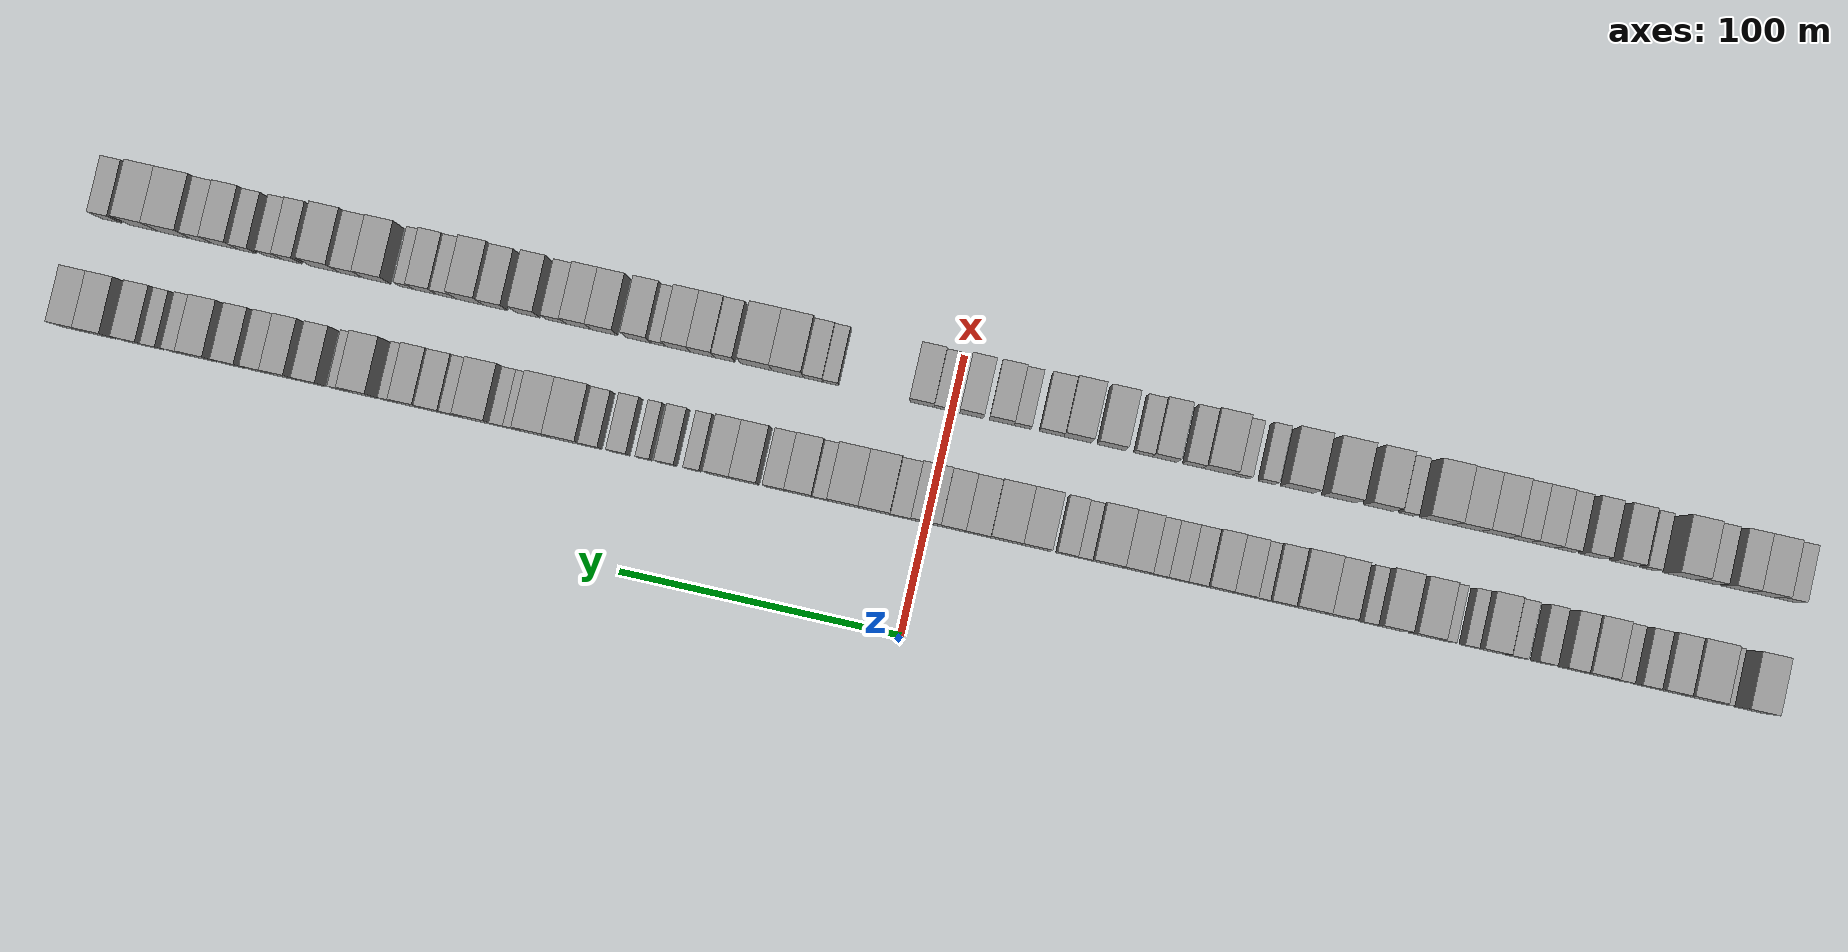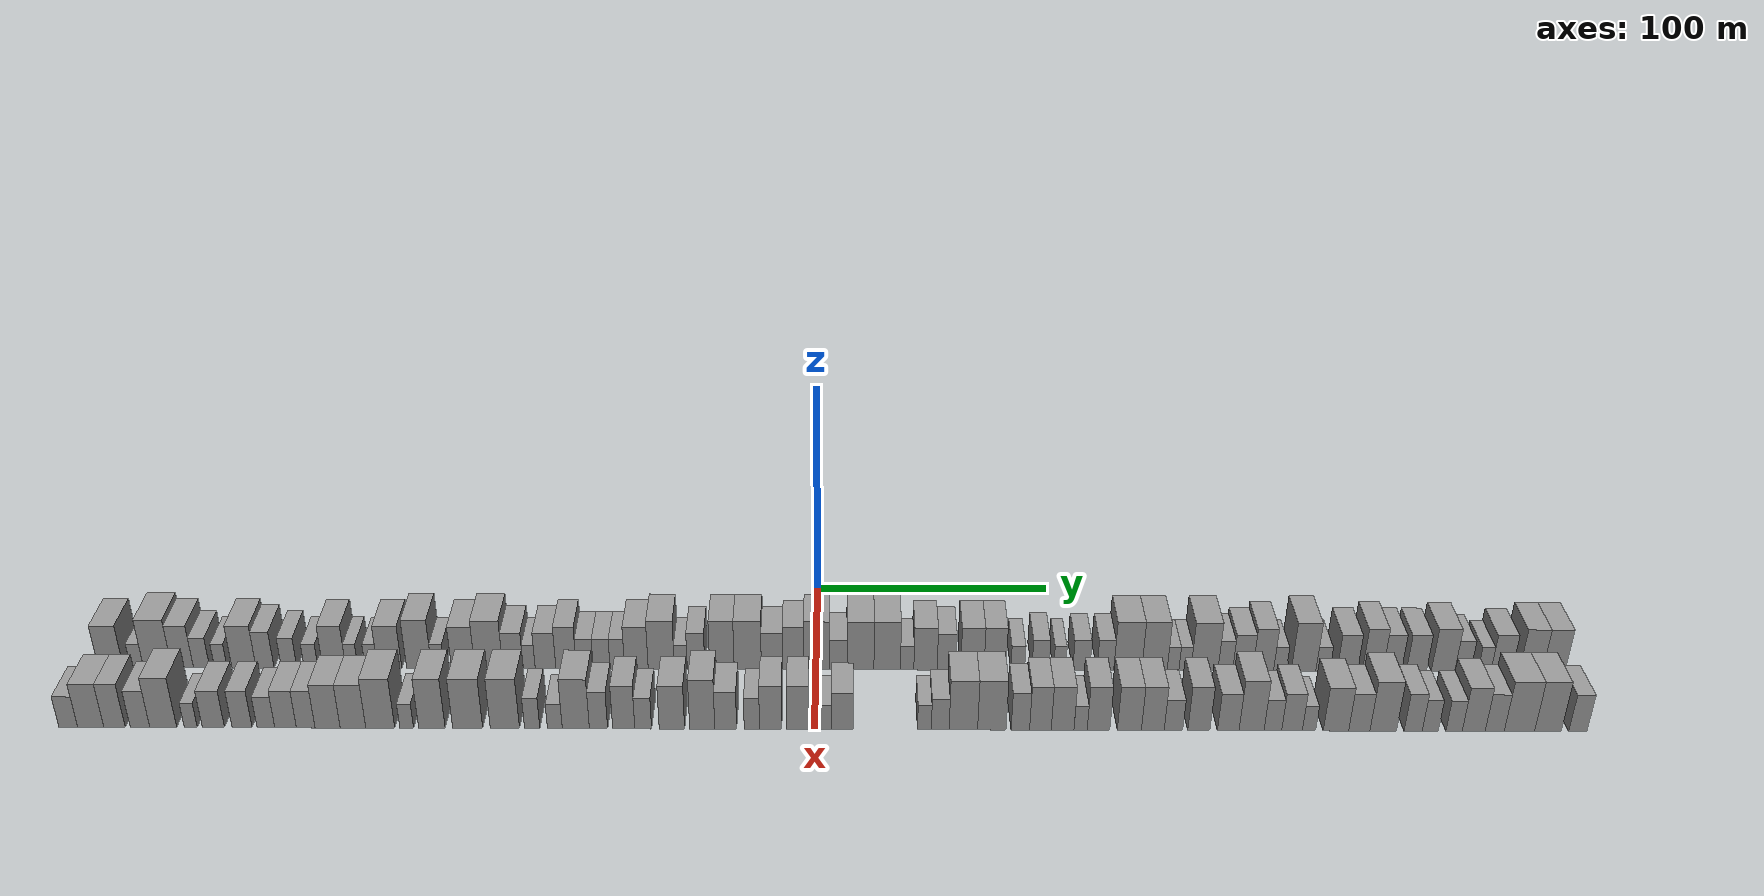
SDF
<sdf version="1.6">
 <world name="default">
  <scene>
   <sky><clouds><speed>12</speed></clouds></sky>
   <ambient>0.4 0.4 0.4 1</ambient>
   <background>0.7 0.7 0.7 1</background>
   <shadows>1</shadows>
  </scene>
  <gravity>0 0 -9.8066</gravity>
  <magnetic_field>6e-06 2.3e-05 -4.2e-05</magnetic_field>
  <physics default="0" name="default_physics" type="ode">
   <ode>
    <solver>
     <type>quick</type>
     <iters>10</iters>
     <sor>1.0</sor>
     <use_dynamic_moi_rescaling>0</use_dynamic_moi_rescaling>
    </solver>
    <constraints>
     <cfm>0</cfm>
     <erp>0.2</erp>
     <contact_max_correcting_vel>100</contact_max_correcting_vel>
     <contact_surface_layer>0.001</contact_surface_layer>
    </constraints>
   </ode>
   <max_step_size>0.004</max_step_size>
   <real_time_factor>1</real_time_factor>
   <real_time_update_rate>250</real_time_update_rate>
  </physics>
  <light name="sun" type="directional">
   <pose>0 0 10 0 0 0</pose>
   <diffuse>0.8 0.8 0.8 1</diffuse>
   <specular>0.2 0.2 0.2 1</specular>
   <attenuation>
    <range>1000</range>
    <constant>0.9</constant>
    <linear>0.01</linear>
    <quadratic>0.001</quadratic>
   </attenuation>
   <direction>-0.5 0.1 -0.9</direction>
  </light>
  <model name="building_1">
   <static>1</static>
   <pose>50.0000 -291.7984 0 0.000000 0.000000 0.000000</pose>
   <link name="link">
    <pose>0 0 10.50 0 0 0</pose>
    <collision name="collision"><geometry><box><size>20.0000 10.4033 21.0000</size></box></geometry></collision>
    <visual name="visual">
     <cast_shadows>0</cast_shadows>
     <geometry><box><size>20.0000 10.4033 21.0000</size></box></geometry>
     <material>
      <script>
       <uri>model://grey_wall/materials/scripts</uri>
       <uri>model://grey_wall/materials/textures</uri>
       <name>vrc/grey_wall</name>
      </script>
     </material>
    </visual>
   </link>
  </model>
  <model name="building_2">
   <static>1</static>
   <pose>50.0000 -280.9232 0 0.000000 0.000000 0.000000</pose>
   <link name="link">
    <pose>0 0 6.00 0 0 0</pose>
    <collision name="collision"><geometry><box><size>20.0000 5.3470 12.0000</size></box></geometry></collision>
    <visual name="visual">
     <cast_shadows>0</cast_shadows>
     <geometry><box><size>20.0000 5.3470 12.0000</size></box></geometry>
     <material>
      <script>
       <uri>model://grey_wall/materials/scripts</uri>
       <uri>model://grey_wall/materials/textures</uri>
       <name>vrc/grey_wall</name>
      </script>
     </material>
    </visual>
   </link>
  </model>
  <model name="building_3">
   <static>1</static>
   <pose>50.0000 -272.3910 0 0.000000 0.000000 0.000000</pose>
   <link name="link">
    <pose>0 0 12.00 0 0 0</pose>
    <collision name="collision"><geometry><box><size>20.0000 11.7176 24.0000</size></box></geometry></collision>
    <visual name="visual">
     <cast_shadows>0</cast_shadows>
     <geometry><box><size>20.0000 11.7176 24.0000</size></box></geometry>
     <material>
      <script>
       <uri>model://grey_wall/materials/scripts</uri>
       <uri>model://grey_wall/materials/textures</uri>
       <name>vrc/grey_wall</name>
      </script>
     </material>
    </visual>
   </link>
  </model>
  <model name="building_4">
   <static>1</static>
   <pose>50.0000 -262.0434 0 0.000000 0.000000 0.000000</pose>
   <link name="link">
    <pose>0 0 10.50 0 0 0</pose>
    <collision name="collision"><geometry><box><size>20.0000 8.9775 21.0000</size></box></geometry></collision>
    <visual name="visual">
     <cast_shadows>0</cast_shadows>
     <geometry><box><size>20.0000 8.9775 21.0000</size></box></geometry>
     <material>
      <script>
       <uri>model://grey_wall/materials/scripts</uri>
       <uri>model://grey_wall/materials/textures</uri>
       <name>vrc/grey_wall</name>
      </script>
     </material>
    </visual>
   </link>
  </model>
  <model name="building_5">
   <static>1</static>
   <pose>50.0000 -254.2005 0 0.000000 0.000000 0.000000</pose>
   <link name="link">
    <pose>0 0 7.50 0 0 0</pose>
    <collision name="collision"><geometry><box><size>20.0000 6.7083 15.0000</size></box></geometry></collision>
    <visual name="visual">
     <cast_shadows>0</cast_shadows>
     <geometry><box><size>20.0000 6.7083 15.0000</size></box></geometry>
     <material>
      <script>
       <uri>model://grey_wall/materials/scripts</uri>
       <uri>model://grey_wall/materials/textures</uri>
       <name>vrc/grey_wall</name>
      </script>
     </material>
    </visual>
   </link>
  </model>
  <model name="building_6">
   <static>1</static>
   <pose>50.0000 -246.2385 0 0.000000 0.000000 0.000000</pose>
   <link name="link">
    <pose>0 0 6.00 0 0 0</pose>
    <collision name="collision"><geometry><box><size>20.0000 5.2157 12.0000</size></box></geometry></collision>
    <visual name="visual">
     <cast_shadows>0</cast_shadows>
     <geometry><box><size>20.0000 5.2157 12.0000</size></box></geometry>
     <material>
      <script>
       <uri>model://grey_wall/materials/scripts</uri>
       <uri>model://grey_wall/materials/textures</uri>
       <name>vrc/grey_wall</name>
      </script>
     </material>
    </visual>
   </link>
  </model>
  <model name="building_7">
   <static>1</static>
   <pose>50.0000 -236.6326 0 0.000000 0.000000 0.000000</pose>
   <link name="link">
    <pose>0 0 10.50 0 0 0</pose>
    <collision name="collision"><geometry><box><size>20.0000 9.9960 21.0000</size></box></geometry></collision>
    <visual name="visual">
     <cast_shadows>0</cast_shadows>
     <geometry><box><size>20.0000 9.9960 21.0000</size></box></geometry>
     <material>
      <script>
       <uri>model://grey_wall/materials/scripts</uri>
       <uri>model://grey_wall/materials/textures</uri>
       <name>vrc/grey_wall</name>
      </script>
     </material>
    </visual>
   </link>
  </model>
  <model name="building_8">
   <static>1</static>
   <pose>50.0000 -227.9022 0 0.000000 0.000000 0.000000</pose>
   <link name="link">
    <pose>0 0 9.00 0 0 0</pose>
    <collision name="collision"><geometry><box><size>20.0000 7.4647 18.0000</size></box></geometry></collision>
    <visual name="visual">
     <cast_shadows>0</cast_shadows>
     <geometry><box><size>20.0000 7.4647 18.0000</size></box></geometry>
     <material>
      <script>
       <uri>model://grey_wall/materials/scripts</uri>
       <uri>model://grey_wall/materials/textures</uri>
       <name>vrc/grey_wall</name>
      </script>
     </material>
    </visual>
   </link>
  </model>
  <model name="building_9">
   <static>1</static>
   <pose>50.0000 -217.9358 0 0.000000 0.000000 0.000000</pose>
   <link name="link">
    <pose>0 0 7.50 0 0 0</pose>
    <collision name="collision"><geometry><box><size>20.0000 6.4683 15.0000</size></box></geometry></collision>
    <visual name="visual">
     <cast_shadows>0</cast_shadows>
     <geometry><box><size>20.0000 6.4683 15.0000</size></box></geometry>
     <material>
      <script>
       <uri>model://grey_wall/materials/scripts</uri>
       <uri>model://grey_wall/materials/textures</uri>
       <name>vrc/grey_wall</name>
      </script>
     </material>
    </visual>
   </link>
  </model>
  <model name="building_10">
   <static>1</static>
   <pose>50.0000 -208.8359 0 0.000000 0.000000 0.000000</pose>
   <link name="link">
    <pose>0 0 6.00 0 0 0</pose>
    <collision name="collision"><geometry><box><size>20.0000 5.7314 12.0000</size></box></geometry></collision>
    <visual name="visual">
     <cast_shadows>0</cast_shadows>
     <geometry><box><size>20.0000 5.7314 12.0000</size></box></geometry>
     <material>
      <script>
       <uri>model://grey_wall/materials/scripts</uri>
       <uri>model://grey_wall/materials/textures</uri>
       <name>vrc/grey_wall</name>
      </script>
     </material>
    </visual>
   </link>
  </model>
  <model name="building_11">
   <static>1</static>
   <pose>50.0000 -199.2077 0 0.000000 0.000000 0.000000</pose>
   <link name="link">
    <pose>0 0 10.50 0 0 0</pose>
    <collision name="collision"><geometry><box><size>20.0000 9.5249 21.0000</size></box></geometry></collision>
    <visual name="visual">
     <cast_shadows>0</cast_shadows>
     <geometry><box><size>20.0000 9.5249 21.0000</size></box></geometry>
     <material>
      <script>
       <uri>model://grey_wall/materials/scripts</uri>
       <uri>model://grey_wall/materials/textures</uri>
       <name>vrc/grey_wall</name>
      </script>
     </material>
    </visual>
   </link>
  </model>
  <model name="building_12">
   <static>1</static>
   <pose>50.0000 -191.9415 0 0.000000 0.000000 0.000000</pose>
   <link name="link">
    <pose>0 0 6.00 0 0 0</pose>
    <collision name="collision"><geometry><box><size>20.0000 5.0075 12.0000</size></box></geometry></collision>
    <visual name="visual">
     <cast_shadows>0</cast_shadows>
     <geometry><box><size>20.0000 5.0075 12.0000</size></box></geometry>
     <material>
      <script>
       <uri>model://grey_wall/materials/scripts</uri>
       <uri>model://grey_wall/materials/textures</uri>
       <name>vrc/grey_wall</name>
      </script>
     </material>
    </visual>
   </link>
  </model>
  <model name="building_13">
   <static>1</static>
   <pose>50.0000 -183.9053 0 0.000000 0.000000 0.000000</pose>
   <link name="link">
    <pose>0 0 6.00 0 0 0</pose>
    <collision name="collision"><geometry><box><size>20.0000 5.0648 12.0000</size></box></geometry></collision>
    <visual name="visual">
     <cast_shadows>0</cast_shadows>
     <geometry><box><size>20.0000 5.0648 12.0000</size></box></geometry>
     <material>
      <script>
       <uri>model://grey_wall/materials/scripts</uri>
       <uri>model://grey_wall/materials/textures</uri>
       <name>vrc/grey_wall</name>
      </script>
     </material>
    </visual>
   </link>
  </model>
  <model name="building_14">
   <static>1</static>
   <pose>50.0000 -176.3470 0 0.000000 0.000000 0.000000</pose>
   <link name="link">
    <pose>0 0 10.50 0 0 0</pose>
    <collision name="collision"><geometry><box><size>20.0000 10.0518 21.0000</size></box></geometry></collision>
    <visual name="visual">
     <cast_shadows>0</cast_shadows>
     <geometry><box><size>20.0000 10.0518 21.0000</size></box></geometry>
     <material>
      <script>
       <uri>model://grey_wall/materials/scripts</uri>
       <uri>model://grey_wall/materials/textures</uri>
       <name>vrc/grey_wall</name>
      </script>
     </material>
    </visual>
   </link>
  </model>
  <model name="building_15">
   <static>1</static>
   <pose>50.0000 -164.1499 0 0.000000 0.000000 0.000000</pose>
   <link name="link">
    <pose>0 0 12.00 0 0 0</pose>
    <collision name="collision"><geometry><box><size>20.0000 10.3426 24.0000</size></box></geometry></collision>
    <visual name="visual">
     <cast_shadows>0</cast_shadows>
     <geometry><box><size>20.0000 10.3426 24.0000</size></box></geometry>
     <material>
      <script>
       <uri>model://grey_wall/materials/scripts</uri>
       <uri>model://grey_wall/materials/textures</uri>
       <name>vrc/grey_wall</name>
      </script>
     </material>
    </visual>
   </link>
  </model>
  <model name="building_16">
   <static>1</static>
   <pose>50.0000 -156.3811 0 0.000000 0.000000 0.000000</pose>
   <link name="link">
    <pose>0 0 6.00 0 0 0</pose>
    <collision name="collision"><geometry><box><size>20.0000 5.1948 12.0000</size></box></geometry></collision>
    <visual name="visual">
     <cast_shadows>0</cast_shadows>
     <geometry><box><size>20.0000 5.1948 12.0000</size></box></geometry>
     <material>
      <script>
       <uri>model://grey_wall/materials/scripts</uri>
       <uri>model://grey_wall/materials/textures</uri>
       <name>vrc/grey_wall</name>
      </script>
     </material>
    </visual>
   </link>
  </model>
  <model name="building_17">
   <static>1</static>
   <pose>50.0000 -145.9532 0 0.000000 0.000000 0.000000</pose>
   <link name="link">
    <pose>0 0 10.50 0 0 0</pose>
    <collision name="collision"><geometry><box><size>20.0000 9.6611 21.0000</size></box></geometry></collision>
    <visual name="visual">
     <cast_shadows>0</cast_shadows>
     <geometry><box><size>20.0000 9.6611 21.0000</size></box></geometry>
     <material>
      <script>
       <uri>model://grey_wall/materials/scripts</uri>
       <uri>model://grey_wall/materials/textures</uri>
       <name>vrc/grey_wall</name>
      </script>
     </material>
    </visual>
   </link>
  </model>
  <model name="building_18">
   <static>1</static>
   <pose>50.0000 -135.3062 0 0.000000 0.000000 0.000000</pose>
   <link name="link">
    <pose>0 0 12.00 0 0 0</pose>
    <collision name="collision"><geometry><box><size>20.0000 11.6329 24.0000</size></box></geometry></collision>
    <visual name="visual">
     <cast_shadows>0</cast_shadows>
     <geometry><box><size>20.0000 11.6329 24.0000</size></box></geometry>
     <material>
      <script>
       <uri>model://grey_wall/materials/scripts</uri>
       <uri>model://grey_wall/materials/textures</uri>
       <name>vrc/grey_wall</name>
      </script>
     </material>
    </visual>
   </link>
  </model>
  <model name="building_19">
   <static>1</static>
   <pose>50.0000 -125.2963 0 0.000000 0.000000 0.000000</pose>
   <link name="link">
    <pose>0 0 9.00 0 0 0</pose>
    <collision name="collision"><geometry><box><size>20.0000 8.3871 18.0000</size></box></geometry></collision>
    <visual name="visual">
     <cast_shadows>0</cast_shadows>
     <geometry><box><size>20.0000 8.3871 18.0000</size></box></geometry>
     <material>
      <script>
       <uri>model://grey_wall/materials/scripts</uri>
       <uri>model://grey_wall/materials/textures</uri>
       <name>vrc/grey_wall</name>
      </script>
     </material>
    </visual>
   </link>
  </model>
  <model name="building_20">
   <static>1</static>
   <pose>50.0000 -118.6462 0 0.000000 0.000000 0.000000</pose>
   <link name="link">
    <pose>0 0 6.00 0 0 0</pose>
    <collision name="collision"><geometry><box><size>20.0000 4.9131 12.0000</size></box></geometry></collision>
    <visual name="visual">
     <cast_shadows>0</cast_shadows>
     <geometry><box><size>20.0000 4.9131 12.0000</size></box></geometry>
     <material>
      <script>
       <uri>model://grey_wall/materials/scripts</uri>
       <uri>model://grey_wall/materials/textures</uri>
       <name>vrc/grey_wall</name>
      </script>
     </material>
    </visual>
   </link>
  </model>
  <model name="building_21">
   <static>1</static>
   <pose>50.0000 -111.9000 0 0.000000 0.000000 0.000000</pose>
   <link name="link">
    <pose>0 0 9.00 0 0 0</pose>
    <collision name="collision"><geometry><box><size>20.0000 8.5792 18.0000</size></box></geometry></collision>
    <visual name="visual">
     <cast_shadows>0</cast_shadows>
     <geometry><box><size>20.0000 8.5792 18.0000</size></box></geometry>
     <material>
      <script>
       <uri>model://grey_wall/materials/scripts</uri>
       <uri>model://grey_wall/materials/textures</uri>
       <name>vrc/grey_wall</name>
      </script>
     </material>
    </visual>
   </link>
  </model>
  <model name="building_22">
   <static>1</static>
   <pose>50.0000 -103.3777 0 0.000000 0.000000 0.000000</pose>
   <link name="link">
    <pose>0 0 10.50 0 0 0</pose>
    <collision name="collision"><geometry><box><size>20.0000 8.4652 21.0000</size></box></geometry></collision>
    <visual name="visual">
     <cast_shadows>0</cast_shadows>
     <geometry><box><size>20.0000 8.4652 21.0000</size></box></geometry>
     <material>
      <script>
       <uri>model://grey_wall/materials/scripts</uri>
       <uri>model://grey_wall/materials/textures</uri>
       <name>vrc/grey_wall</name>
      </script>
     </material>
    </visual>
   </link>
  </model>
  <model name="building_23">
   <static>1</static>
   <pose>50.0000 -95.6547 0 0.000000 0.000000 0.000000</pose>
   <link name="link">
    <pose>0 0 7.50 0 0 0</pose>
    <collision name="collision"><geometry><box><size>20.0000 6.9809 15.0000</size></box></geometry></collision>
    <visual name="visual">
     <cast_shadows>0</cast_shadows>
     <geometry><box><size>20.0000 6.9809 15.0000</size></box></geometry>
     <material>
      <script>
       <uri>model://grey_wall/materials/scripts</uri>
       <uri>model://grey_wall/materials/textures</uri>
       <name>vrc/grey_wall</name>
      </script>
     </material>
    </visual>
   </link>
  </model>
  <model name="building_24">
   <static>1</static>
   <pose>50.0000 -88.6900 0 0.000000 0.000000 0.000000</pose>
   <link name="link">
    <pose>0 0 7.50 0 0 0</pose>
    <collision name="collision"><geometry><box><size>20.0000 6.9484 15.0000</size></box></geometry></collision>
    <visual name="visual">
     <cast_shadows>0</cast_shadows>
     <geometry><box><size>20.0000 6.9484 15.0000</size></box></geometry>
     <material>
      <script>
       <uri>model://grey_wall/materials/scripts</uri>
       <uri>model://grey_wall/materials/textures</uri>
       <name>vrc/grey_wall</name>
      </script>
     </material>
    </visual>
   </link>
  </model>
  <model name="building_25">
   <static>1</static>
   <pose>50.0000 -82.2115 0 0.000000 0.000000 0.000000</pose>
   <link name="link">
    <pose>0 0 7.50 0 0 0</pose>
    <collision name="collision"><geometry><box><size>20.0000 6.0088 15.0000</size></box></geometry></collision>
    <visual name="visual">
     <cast_shadows>0</cast_shadows>
     <geometry><box><size>20.0000 6.0088 15.0000</size></box></geometry>
     <material>
      <script>
       <uri>model://grey_wall/materials/scripts</uri>
       <uri>model://grey_wall/materials/textures</uri>
       <name>vrc/grey_wall</name>
      </script>
     </material>
    </visual>
   </link>
  </model>
  <model name="building_26">
   <static>1</static>
   <pose>50.0000 -74.3394 0 0.000000 0.000000 0.000000</pose>
   <link name="link">
    <pose>0 0 10.50 0 0 0</pose>
    <collision name="collision"><geometry><box><size>20.0000 9.7353 21.0000</size></box></geometry></collision>
    <visual name="visual">
     <cast_shadows>0</cast_shadows>
     <geometry><box><size>20.0000 9.7353 21.0000</size></box></geometry>
     <material>
      <script>
       <uri>model://grey_wall/materials/scripts</uri>
       <uri>model://grey_wall/materials/textures</uri>
       <name>vrc/grey_wall</name>
      </script>
     </material>
    </visual>
   </link>
  </model>
  <model name="building_27">
   <static>1</static>
   <pose>50.0000 -64.0591 0 0.000000 0.000000 0.000000</pose>
   <link name="link">
    <pose>0 0 12.00 0 0 0</pose>
    <collision name="collision"><geometry><box><size>20.0000 10.8253 24.0000</size></box></geometry></collision>
    <visual name="visual">
     <cast_shadows>0</cast_shadows>
     <geometry><box><size>20.0000 10.8253 24.0000</size></box></geometry>
     <material>
      <script>
       <uri>model://grey_wall/materials/scripts</uri>
       <uri>model://grey_wall/materials/textures</uri>
       <name>vrc/grey_wall</name>
      </script>
     </material>
    </visual>
   </link>
  </model>
  <model name="building_28">
   <static>1</static>
   <pose>50.0000 -55.9848 0 0.000000 0.000000 0.000000</pose>
   <link name="link">
    <pose>0 0 6.00 0 0 0</pose>
    <collision name="collision"><geometry><box><size>20.0000 5.3234 12.0000</size></box></geometry></collision>
    <visual name="visual">
     <cast_shadows>0</cast_shadows>
     <geometry><box><size>20.0000 5.3234 12.0000</size></box></geometry>
     <material>
      <script>
       <uri>model://grey_wall/materials/scripts</uri>
       <uri>model://grey_wall/materials/textures</uri>
       <name>vrc/grey_wall</name>
      </script>
     </material>
    </visual>
   </link>
  </model>
  <model name="building_29">
   <static>1</static>
   <pose>50.0000 -49.6872 0 0.000000 0.000000 0.000000</pose>
   <link name="link">
    <pose>0 0 9.00 0 0 0</pose>
    <collision name="collision"><geometry><box><size>20.0000 7.2717 18.0000</size></box></geometry></collision>
    <visual name="visual">
     <cast_shadows>0</cast_shadows>
     <geometry><box><size>20.0000 7.2717 18.0000</size></box></geometry>
     <material>
      <script>
       <uri>model://grey_wall/materials/scripts</uri>
       <uri>model://grey_wall/materials/textures</uri>
       <name>vrc/grey_wall</name>
      </script>
     </material>
    </visual>
   </link>
  </model>
  <model name="building_30">
   <static>1</static>
   <pose>50.0000 -39.0021 0 0.000000 0.000000 0.000000</pose>
   <link name="link">
    <pose>0 0 12.00 0 0 0</pose>
    <collision name="collision"><geometry><box><size>20.0000 10.0985 24.0000</size></box></geometry></collision>
    <visual name="visual">
     <cast_shadows>0</cast_shadows>
     <geometry><box><size>20.0000 10.0985 24.0000</size></box></geometry>
     <material>
      <script>
       <uri>model://grey_wall/materials/scripts</uri>
       <uri>model://grey_wall/materials/textures</uri>
       <name>vrc/grey_wall</name>
      </script>
     </material>
    </visual>
   </link>
  </model>
  <model name="building_31">
   <static>1</static>
   <pose>50.0000 -28.3409 0 0.000000 0.000000 0.000000</pose>
   <link name="link">
    <pose>0 0 12.00 0 0 0</pose>
    <collision name="collision"><geometry><box><size>20.0000 11.2239 24.0000</size></box></geometry></collision>
    <visual name="visual">
     <cast_shadows>0</cast_shadows>
     <geometry><box><size>20.0000 11.2239 24.0000</size></box></geometry>
     <material>
      <script>
       <uri>model://grey_wall/materials/scripts</uri>
       <uri>model://grey_wall/materials/textures</uri>
       <name>vrc/grey_wall</name>
      </script>
     </material>
    </visual>
   </link>
  </model>
  <model name="building_32">
   <static>1</static>
   <pose>50.0000 -18.3390 0 0.000000 0.000000 0.000000</pose>
   <link name="link">
    <pose>0 0 9.00 0 0 0</pose>
    <collision name="collision"><geometry><box><size>20.0000 8.7800 18.0000</size></box></geometry></collision>
    <visual name="visual">
     <cast_shadows>0</cast_shadows>
     <geometry><box><size>20.0000 8.7800 18.0000</size></box></geometry>
     <material>
      <script>
       <uri>model://grey_wall/materials/scripts</uri>
       <uri>model://grey_wall/materials/textures</uri>
       <name>vrc/grey_wall</name>
      </script>
     </material>
    </visual>
   </link>
  </model>
  <model name="building_33">
   <static>1</static>
   <pose>50.0000 -9.5903 0 0.000000 0.000000 0.000000</pose>
   <link name="link">
    <pose>0 0 10.50 0 0 0</pose>
    <collision name="collision"><geometry><box><size>20.0000 8.7173 21.0000</size></box></geometry></collision>
    <visual name="visual">
     <cast_shadows>0</cast_shadows>
     <geometry><box><size>20.0000 8.7173 21.0000</size></box></geometry>
     <material>
      <script>
       <uri>model://grey_wall/materials/scripts</uri>
       <uri>model://grey_wall/materials/textures</uri>
       <name>vrc/grey_wall</name>
      </script>
     </material>
    </visual>
   </link>
  </model>
  <model name="building_34">
   <static>1</static>
   <pose>50.0000 0.0776 0 0.000000 0.000000 0.000000</pose>
   <link name="link">
    <pose>0 0 12.00 0 0 0</pose>
    <collision name="collision"><geometry><box><size>20.0000 10.6185 24.0000</size></box></geometry></collision>
    <visual name="visual">
     <cast_shadows>0</cast_shadows>
     <geometry><box><size>20.0000 10.6185 24.0000</size></box></geometry>
     <material>
      <script>
       <uri>model://grey_wall/materials/scripts</uri>
       <uri>model://grey_wall/materials/textures</uri>
       <name>vrc/grey_wall</name>
      </script>
     </material>
    </visual>
   </link>
  </model>
  <model name="building_35">
   <static>1</static>
   <pose>50.0000 8.9988 0 0.000000 0.000000 0.000000</pose>
   <link name="link">
    <pose>0 0 7.50 0 0 0</pose>
    <collision name="collision"><geometry><box><size>20.0000 7.2240 15.0000</size></box></geometry></collision>
    <visual name="visual">
     <cast_shadows>0</cast_shadows>
     <geometry><box><size>20.0000 7.2240 15.0000</size></box></geometry>
     <material>
      <script>
       <uri>model://grey_wall/materials/scripts</uri>
       <uri>model://grey_wall/materials/textures</uri>
       <name>vrc/grey_wall</name>
      </script>
     </material>
    </visual>
   </link>
  </model>
  <model name="building_36">
   <static>1</static>
   <pose>50.0000 18.1661 0 0.000000 0.000000 0.000000</pose>
   <link name="link">
    <pose>0 0 12.00 0 0 0</pose>
    <collision name="collision"><geometry><box><size>20.0000 11.1104 24.0000</size></box></geometry></collision>
    <visual name="visual">
     <cast_shadows>0</cast_shadows>
     <geometry><box><size>20.0000 11.1104 24.0000</size></box></geometry>
     <material>
      <script>
       <uri>model://grey_wall/materials/scripts</uri>
       <uri>model://grey_wall/materials/textures</uri>
       <name>vrc/grey_wall</name>
      </script>
     </material>
    </visual>
   </link>
  </model>
  <model name="building_37">
   <static>1</static>
   <pose>50.0000 29.1896 0 0.000000 0.000000 0.000000</pose>
   <link name="link">
    <pose>0 0 12.00 0 0 0</pose>
    <collision name="collision"><geometry><box><size>20.0000 10.9366 24.0000</size></box></geometry></collision>
    <visual name="visual">
     <cast_shadows>0</cast_shadows>
     <geometry><box><size>20.0000 10.9366 24.0000</size></box></geometry>
     <material>
      <script>
       <uri>model://grey_wall/materials/scripts</uri>
       <uri>model://grey_wall/materials/textures</uri>
       <name>vrc/grey_wall</name>
      </script>
     </material>
    </visual>
   </link>
  </model>
  <model name="building_38">
   <static>1</static>
   <pose>50.0000 37.4352 0 0.000000 0.000000 0.000000</pose>
   <link name="link">
    <pose>0 0 6.00 0 0 0</pose>
    <collision name="collision"><geometry><box><size>20.0000 5.5546 12.0000</size></box></geometry></collision>
    <visual name="visual">
     <cast_shadows>0</cast_shadows>
     <geometry><box><size>20.0000 5.5546 12.0000</size></box></geometry>
     <material>
      <script>
       <uri>model://grey_wall/materials/scripts</uri>
       <uri>model://grey_wall/materials/textures</uri>
       <name>vrc/grey_wall</name>
      </script>
     </material>
    </visual>
   </link>
  </model>
  <model name="building_39">
   <static>1</static>
   <pose>50.0000 45.0216 0 0.000000 0.000000 0.000000</pose>
   <link name="link">
    <pose>0 0 10.50 0 0 0</pose>
    <collision name="collision"><geometry><box><size>20.0000 9.6183 21.0000</size></box></geometry></collision>
    <visual name="visual">
     <cast_shadows>0</cast_shadows>
     <geometry><box><size>20.0000 9.6183 21.0000</size></box></geometry>
     <material>
      <script>
       <uri>model://grey_wall/materials/scripts</uri>
       <uri>model://grey_wall/materials/textures</uri>
       <name>vrc/grey_wall</name>
      </script>
     </material>
    </visual>
   </link>
  </model>
  <model name="building_40">
   <static>1</static>
   <pose>50.0000 53.6917 0 0.000000 0.000000 0.000000</pose>
   <link name="link">
    <pose>0 0 9.00 0 0 0</pose>
    <collision name="collision"><geometry><box><size>20.0000 7.7219 18.0000</size></box></geometry></collision>
    <visual name="visual">
     <cast_shadows>0</cast_shadows>
     <geometry><box><size>20.0000 7.7219 18.0000</size></box></geometry>
     <material>
      <script>
       <uri>model://grey_wall/materials/scripts</uri>
       <uri>model://grey_wall/materials/textures</uri>
       <name>vrc/grey_wall</name>
      </script>
     </material>
    </visual>
   </link>
  </model>
  <model name="building_41">
   <static>1</static>
   <pose>50.0000 64.3561 0 0.000000 0.000000 0.000000</pose>
   <link name="link">
    <pose>0 0 10.50 0 0 0</pose>
    <collision name="collision"><geometry><box><size>20.0000 9.6068 21.0000</size></box></geometry></collision>
    <visual name="visual">
     <cast_shadows>0</cast_shadows>
     <geometry><box><size>20.0000 9.6068 21.0000</size></box></geometry>
     <material>
      <script>
       <uri>model://grey_wall/materials/scripts</uri>
       <uri>model://grey_wall/materials/textures</uri>
       <name>vrc/grey_wall</name>
      </script>
     </material>
    </visual>
   </link>
  </model>
  <model name="building_42">
   <static>1</static>
   <pose>50.0000 73.6886 0 0.000000 0.000000 0.000000</pose>
   <link name="link">
    <pose>0 0 10.50 0 0 0</pose>
    <collision name="collision"><geometry><box><size>20.0000 9.0583 21.0000</size></box></geometry></collision>
    <visual name="visual">
     <cast_shadows>0</cast_shadows>
     <geometry><box><size>20.0000 9.0583 21.0000</size></box></geometry>
     <material>
      <script>
       <uri>model://grey_wall/materials/scripts</uri>
       <uri>model://grey_wall/materials/textures</uri>
       <name>vrc/grey_wall</name>
      </script>
     </material>
    </visual>
   </link>
  </model>
  <model name="building_43">
   <static>1</static>
   <pose>50.0000 83.0665 0 0.000000 0.000000 0.000000</pose>
   <link name="link">
    <pose>0 0 6.00 0 0 0</pose>
    <collision name="collision"><geometry><box><size>20.0000 5.6975 12.0000</size></box></geometry></collision>
    <visual name="visual">
     <cast_shadows>0</cast_shadows>
     <geometry><box><size>20.0000 5.6975 12.0000</size></box></geometry>
     <material>
      <script>
       <uri>model://grey_wall/materials/scripts</uri>
       <uri>model://grey_wall/materials/textures</uri>
       <name>vrc/grey_wall</name>
      </script>
     </material>
    </visual>
   </link>
  </model>
  <model name="building_44">
   <static>1</static>
   <pose>50.0000 92.3991 0 0.000000 0.000000 0.000000</pose>
   <link name="link">
    <pose>0 0 7.50 0 0 0</pose>
    <collision name="collision"><geometry><box><size>20.0000 6.9675 15.0000</size></box></geometry></collision>
    <visual name="visual">
     <cast_shadows>0</cast_shadows>
     <geometry><box><size>20.0000 6.9675 15.0000</size></box></geometry>
     <material>
      <script>
       <uri>model://grey_wall/materials/scripts</uri>
       <uri>model://grey_wall/materials/textures</uri>
       <name>vrc/grey_wall</name>
      </script>
     </material>
    </visual>
   </link>
  </model>
  <model name="building_45">
   <static>1</static>
   <pose>50.0000 100.3335 0 0.000000 0.000000 0.000000</pose>
   <link name="link">
    <pose>0 0 6.00 0 0 0</pose>
    <collision name="collision"><geometry><box><size>20.0000 4.9013 12.0000</size></box></geometry></collision>
    <visual name="visual">
     <cast_shadows>0</cast_shadows>
     <geometry><box><size>20.0000 4.9013 12.0000</size></box></geometry>
     <material>
      <script>
       <uri>model://grey_wall/materials/scripts</uri>
       <uri>model://grey_wall/materials/textures</uri>
       <name>vrc/grey_wall</name>
      </script>
     </material>
    </visual>
   </link>
  </model>
  <model name="building_46">
   <static>1</static>
   <pose>50.0000 109.2927 0 0.000000 0.000000 0.000000</pose>
   <link name="link">
    <pose>0 0 7.50 0 0 0</pose>
    <collision name="collision"><geometry><box><size>20.0000 7.0171 15.0000</size></box></geometry></collision>
    <visual name="visual">
     <cast_shadows>0</cast_shadows>
     <geometry><box><size>20.0000 7.0171 15.0000</size></box></geometry>
     <material>
      <script>
       <uri>model://grey_wall/materials/scripts</uri>
       <uri>model://grey_wall/materials/textures</uri>
       <name>vrc/grey_wall</name>
      </script>
     </material>
    </visual>
   </link>
  </model>
  <model name="building_47">
   <static>1</static>
   <pose>50.0000 119.2499 0 0.000000 0.000000 0.000000</pose>
   <link name="link">
    <pose>0 0 7.50 0 0 0</pose>
    <collision name="collision"><geometry><box><size>20.0000 6.8973 15.0000</size></box></geometry></collision>
    <visual name="visual">
     <cast_shadows>0</cast_shadows>
     <geometry><box><size>20.0000 6.8973 15.0000</size></box></geometry>
     <material>
      <script>
       <uri>model://grey_wall/materials/scripts</uri>
       <uri>model://grey_wall/materials/textures</uri>
       <name>vrc/grey_wall</name>
      </script>
     </material>
    </visual>
   </link>
  </model>
  <model name="building_48">
   <static>1</static>
   <pose>50.0000 128.4624 0 0.000000 0.000000 0.000000</pose>
   <link name="link">
    <pose>0 0 12.00 0 0 0</pose>
    <collision name="collision"><geometry><box><size>20.0000 11.5277 24.0000</size></box></geometry></collision>
    <visual name="visual">
     <cast_shadows>0</cast_shadows>
     <geometry><box><size>20.0000 11.5277 24.0000</size></box></geometry>
     <material>
      <script>
       <uri>model://grey_wall/materials/scripts</uri>
       <uri>model://grey_wall/materials/textures</uri>
       <name>vrc/grey_wall</name>
      </script>
     </material>
    </visual>
   </link>
  </model>
  <model name="building_49">
   <static>1</static>
   <pose>50.0000 139.4793 0 0.000000 0.000000 0.000000</pose>
   <link name="link">
    <pose>0 0 12.00 0 0 0</pose>
    <collision name="collision"><geometry><box><size>20.0000 10.5061 24.0000</size></box></geometry></collision>
    <visual name="visual">
     <cast_shadows>0</cast_shadows>
     <geometry><box><size>20.0000 10.5061 24.0000</size></box></geometry>
     <material>
      <script>
       <uri>model://grey_wall/materials/scripts</uri>
       <uri>model://grey_wall/materials/textures</uri>
       <name>vrc/grey_wall</name>
      </script>
     </material>
    </visual>
   </link>
  </model>
  <model name="building_50">
   <static>1</static>
   <pose>50.0000 147.1535 0 0.000000 0.000000 0.000000</pose>
   <link name="link">
    <pose>0 0 6.00 0 0 0</pose>
    <collision name="collision"><geometry><box><size>20.0000 4.8423 12.0000</size></box></geometry></collision>
    <visual name="visual">
     <cast_shadows>0</cast_shadows>
     <geometry><box><size>20.0000 4.8423 12.0000</size></box></geometry>
     <material>
      <script>
       <uri>model://grey_wall/materials/scripts</uri>
       <uri>model://grey_wall/materials/textures</uri>
       <name>vrc/grey_wall</name>
      </script>
     </material>
    </visual>
   </link>
  </model>
  <model name="building_51">
   <static>1</static>
   <pose>50.0000 152.0326 0 0.000000 0.000000 0.000000</pose>
   <link name="link">
    <pose>0 0 6.00 0 0 0</pose>
    <collision name="collision"><geometry><box><size>20.0000 4.9160 12.0000</size></box></geometry></collision>
    <visual name="visual">
     <cast_shadows>0</cast_shadows>
     <geometry><box><size>20.0000 4.9160 12.0000</size></box></geometry>
     <material>
      <script>
       <uri>model://grey_wall/materials/scripts</uri>
       <uri>model://grey_wall/materials/textures</uri>
       <name>vrc/grey_wall</name>
      </script>
     </material>
    </visual>
   </link>
  </model>
  <model name="building_52">
   <static>1</static>
   <pose>50.0000 160.0803 0 0.000000 0.000000 0.000000</pose>
   <link name="link">
    <pose>0 0 12.00 0 0 0</pose>
    <collision name="collision"><geometry><box><size>20.0000 11.1795 24.0000</size></box></geometry></collision>
    <visual name="visual">
     <cast_shadows>0</cast_shadows>
     <geometry><box><size>20.0000 11.1795 24.0000</size></box></geometry>
     <material>
      <script>
       <uri>model://grey_wall/materials/scripts</uri>
       <uri>model://grey_wall/materials/textures</uri>
       <name>vrc/grey_wall</name>
      </script>
     </material>
    </visual>
   </link>
  </model>
  <model name="building_53">
   <static>1</static>
   <pose>50.0000 168.6992 0 0.000000 0.000000 0.000000</pose>
   <link name="link">
    <pose>0 0 7.50 0 0 0</pose>
    <collision name="collision"><geometry><box><size>20.0000 6.0583 15.0000</size></box></geometry></collision>
    <visual name="visual">
     <cast_shadows>0</cast_shadows>
     <geometry><box><size>20.0000 6.0583 15.0000</size></box></geometry>
     <material>
      <script>
       <uri>model://grey_wall/materials/scripts</uri>
       <uri>model://grey_wall/materials/textures</uri>
       <name>vrc/grey_wall</name>
      </script>
     </material>
    </visual>
   </link>
  </model>
  <model name="building_54">
   <static>1</static>
   <pose>50.0000 175.8635 0 0.000000 0.000000 0.000000</pose>
   <link name="link">
    <pose>0 0 9.00 0 0 0</pose>
    <collision name="collision"><geometry><box><size>20.0000 8.2704 18.0000</size></box></geometry></collision>
    <visual name="visual">
     <cast_shadows>0</cast_shadows>
     <geometry><box><size>20.0000 8.2704 18.0000</size></box></geometry>
     <material>
      <script>
       <uri>model://grey_wall/materials/scripts</uri>
       <uri>model://grey_wall/materials/textures</uri>
       <name>vrc/grey_wall</name>
      </script>
     </material>
    </visual>
   </link>
  </model>
  <model name="building_55">
   <static>1</static>
   <pose>50.0000 184.2989 0 0.000000 0.000000 0.000000</pose>
   <link name="link">
    <pose>0 0 10.50 0 0 0</pose>
    <collision name="collision"><geometry><box><size>20.0000 8.6005 21.0000</size></box></geometry></collision>
    <visual name="visual">
     <cast_shadows>0</cast_shadows>
     <geometry><box><size>20.0000 8.6005 21.0000</size></box></geometry>
     <material>
      <script>
       <uri>model://grey_wall/materials/scripts</uri>
       <uri>model://grey_wall/materials/textures</uri>
       <name>vrc/grey_wall</name>
      </script>
     </material>
    </visual>
   </link>
  </model>
  <model name="building_56">
   <static>1</static>
   <pose>50.0000 191.2428 0 0.000000 0.000000 0.000000</pose>
   <link name="link">
    <pose>0 0 6.00 0 0 0</pose>
    <collision name="collision"><geometry><box><size>20.0000 5.2873 12.0000</size></box></geometry></collision>
    <visual name="visual">
     <cast_shadows>0</cast_shadows>
     <geometry><box><size>20.0000 5.2873 12.0000</size></box></geometry>
     <material>
      <script>
       <uri>model://grey_wall/materials/scripts</uri>
       <uri>model://grey_wall/materials/textures</uri>
       <name>vrc/grey_wall</name>
      </script>
     </material>
    </visual>
   </link>
  </model>
  <model name="building_57">
   <static>1</static>
   <pose>50.0000 200.9584 0 0.000000 0.000000 0.000000</pose>
   <link name="link">
    <pose>0 0 12.00 0 0 0</pose>
    <collision name="collision"><geometry><box><size>20.0000 10.1439 24.0000</size></box></geometry></collision>
    <visual name="visual">
     <cast_shadows>0</cast_shadows>
     <geometry><box><size>20.0000 10.1439 24.0000</size></box></geometry>
     <material>
      <script>
       <uri>model://grey_wall/materials/scripts</uri>
       <uri>model://grey_wall/materials/textures</uri>
       <name>vrc/grey_wall</name>
      </script>
     </material>
    </visual>
   </link>
  </model>
  <model name="building_58">
   <static>1</static>
   <pose>50.0000 208.8905 0 0.000000 0.000000 0.000000</pose>
   <link name="link">
    <pose>0 0 6.00 0 0 0</pose>
    <collision name="collision"><geometry><box><size>20.0000 5.7202 12.0000</size></box></geometry></collision>
    <visual name="visual">
     <cast_shadows>0</cast_shadows>
     <geometry><box><size>20.0000 5.7202 12.0000</size></box></geometry>
     <material>
      <script>
       <uri>model://grey_wall/materials/scripts</uri>
       <uri>model://grey_wall/materials/textures</uri>
       <name>vrc/grey_wall</name>
      </script>
     </material>
    </visual>
   </link>
  </model>
  <model name="building_59">
   <static>1</static>
   <pose>50.0000 218.9692 0 0.000000 0.000000 0.000000</pose>
   <link name="link">
    <pose>0 0 9.00 0 0 0</pose>
    <collision name="collision"><geometry><box><size>20.0000 8.4372 18.0000</size></box></geometry></collision>
    <visual name="visual">
     <cast_shadows>0</cast_shadows>
     <geometry><box><size>20.0000 8.4372 18.0000</size></box></geometry>
     <material>
      <script>
       <uri>model://grey_wall/materials/scripts</uri>
       <uri>model://grey_wall/materials/textures</uri>
       <name>vrc/grey_wall</name>
      </script>
     </material>
    </visual>
   </link>
  </model>
  <model name="building_60">
   <static>1</static>
   <pose>50.0000 229.4449 0 0.000000 0.000000 0.000000</pose>
   <link name="link">
    <pose>0 0 10.50 0 0 0</pose>
    <collision name="collision"><geometry><box><size>20.0000 8.5144 21.0000</size></box></geometry></collision>
    <visual name="visual">
     <cast_shadows>0</cast_shadows>
     <geometry><box><size>20.0000 8.5144 21.0000</size></box></geometry>
     <material>
      <script>
       <uri>model://grey_wall/materials/scripts</uri>
       <uri>model://grey_wall/materials/textures</uri>
       <name>vrc/grey_wall</name>
      </script>
     </material>
    </visual>
   </link>
  </model>
  <model name="building_61">
   <static>1</static>
   <pose>50.0000 237.5235 0 0.000000 0.000000 0.000000</pose>
   <link name="link">
    <pose>0 0 9.00 0 0 0</pose>
    <collision name="collision"><geometry><box><size>20.0000 7.6428 18.0000</size></box></geometry></collision>
    <visual name="visual">
     <cast_shadows>0</cast_shadows>
     <geometry><box><size>20.0000 7.6428 18.0000</size></box></geometry>
     <material>
      <script>
       <uri>model://grey_wall/materials/scripts</uri>
       <uri>model://grey_wall/materials/textures</uri>
       <name>vrc/grey_wall</name>
      </script>
     </material>
    </visual>
   </link>
  </model>
  <model name="building_62">
   <static>1</static>
   <pose>50.0000 247.4943 0 0.000000 0.000000 0.000000</pose>
   <link name="link">
    <pose>0 0 9.00 0 0 0</pose>
    <collision name="collision"><geometry><box><size>20.0000 8.2988 18.0000</size></box></geometry></collision>
    <visual name="visual">
     <cast_shadows>0</cast_shadows>
     <geometry><box><size>20.0000 8.2988 18.0000</size></box></geometry>
     <material>
      <script>
       <uri>model://grey_wall/materials/scripts</uri>
       <uri>model://grey_wall/materials/textures</uri>
       <name>vrc/grey_wall</name>
      </script>
     </material>
    </visual>
   </link>
  </model>
  <model name="building_63">
   <static>1</static>
   <pose>50.0000 258.4610 0 0.000000 0.000000 0.000000</pose>
   <link name="link">
    <pose>0 0 10.50 0 0 0</pose>
    <collision name="collision"><geometry><box><size>20.0000 9.6345 21.0000</size></box></geometry></collision>
    <visual name="visual">
     <cast_shadows>0</cast_shadows>
     <geometry><box><size>20.0000 9.6345 21.0000</size></box></geometry>
     <material>
      <script>
       <uri>model://grey_wall/materials/scripts</uri>
       <uri>model://grey_wall/materials/textures</uri>
       <name>vrc/grey_wall</name>
      </script>
     </material>
    </visual>
   </link>
  </model>
  <model name="building_64">
   <static>1</static>
   <pose>50.0000 266.5638 0 0.000000 0.000000 0.000000</pose>
   <link name="link">
    <pose>0 0 7.50 0 0 0</pose>
    <collision name="collision"><geometry><box><size>20.0000 6.5711 15.0000</size></box></geometry></collision>
    <visual name="visual">
     <cast_shadows>0</cast_shadows>
     <geometry><box><size>20.0000 6.5711 15.0000</size></box></geometry>
     <material>
      <script>
       <uri>model://grey_wall/materials/scripts</uri>
       <uri>model://grey_wall/materials/textures</uri>
       <name>vrc/grey_wall</name>
      </script>
     </material>
    </visual>
   </link>
  </model>
  <model name="building_65">
   <static>1</static>
   <pose>50.0000 275.5060 0 0.000000 0.000000 0.000000</pose>
   <link name="link">
    <pose>0 0 6.00 0 0 0</pose>
    <collision name="collision"><geometry><box><size>20.0000 5.3133 12.0000</size></box></geometry></collision>
    <visual name="visual">
     <cast_shadows>0</cast_shadows>
     <geometry><box><size>20.0000 5.3133 12.0000</size></box></geometry>
     <material>
      <script>
       <uri>model://grey_wall/materials/scripts</uri>
       <uri>model://grey_wall/materials/textures</uri>
       <name>vrc/grey_wall</name>
      </script>
     </material>
    </visual>
   </link>
  </model>
  <model name="building_66">
   <static>1</static>
   <pose>50.0000 282.5201 0 0.000000 0.000000 0.000000</pose>
   <link name="link">
    <pose>0 0 9.00 0 0 0</pose>
    <collision name="collision"><geometry><box><size>20.0000 8.7149 18.0000</size></box></geometry></collision>
    <visual name="visual">
     <cast_shadows>0</cast_shadows>
     <geometry><box><size>20.0000 8.7149 18.0000</size></box></geometry>
     <material>
      <script>
       <uri>model://grey_wall/materials/scripts</uri>
       <uri>model://grey_wall/materials/textures</uri>
       <name>vrc/grey_wall</name>
      </script>
     </material>
    </visual>
   </link>
  </model>
  <model name="building_67">
   <static>1</static>
   <pose>50.0000 294.6519 0 0.000000 0.000000 0.000000</pose>
   <link name="link">
    <pose>0 0 10.50 0 0 0</pose>
    <collision name="collision"><geometry><box><size>20.0000 9.5487 21.0000</size></box></geometry></collision>
    <visual name="visual">
     <cast_shadows>0</cast_shadows>
     <geometry><box><size>20.0000 9.5487 21.0000</size></box></geometry>
     <material>
      <script>
       <uri>model://grey_wall/materials/scripts</uri>
       <uri>model://grey_wall/materials/textures</uri>
       <name>vrc/grey_wall</name>
      </script>
     </material>
    </visual>
   </link>
  </model>
  <model name="building_68">
   <static>1</static>
   <pose>50.0000 304.0890 0 0.000000 0.000000 0.000000</pose>
   <link name="link">
    <pose>0 0 10.50 0 0 0</pose>
    <collision name="collision"><geometry><box><size>20.0000 9.3257 21.0000</size></box></geometry></collision>
    <visual name="visual">
     <cast_shadows>0</cast_shadows>
     <geometry><box><size>20.0000 9.3257 21.0000</size></box></geometry>
     <material>
      <script>
       <uri>model://grey_wall/materials/scripts</uri>
       <uri>model://grey_wall/materials/textures</uri>
       <name>vrc/grey_wall</name>
      </script>
     </material>
    </visual>
   </link>
  </model>
  <model name="building_69">
   <static>1</static>
   <pose>90.0000 -296.2783 0 0.000000 0.000000 0.000000</pose>
   <link name="link">
    <pose>0 0 7.50 0 0 0</pose>
    <collision name="collision"><geometry><box><size>20.0000 7.4434 15.0000</size></box></geometry></collision>
    <visual name="visual">
     <cast_shadows>0</cast_shadows>
     <geometry><box><size>20.0000 7.4434 15.0000</size></box></geometry>
     <material>
      <script>
       <uri>model://grey_wall/materials/scripts</uri>
       <uri>model://grey_wall/materials/textures</uri>
       <name>vrc/grey_wall</name>
      </script>
     </material>
    </visual>
   </link>
  </model>
  <model name="building_70">
   <static>1</static>
   <pose>90.0000 -287.3643 0 0.000000 0.000000 0.000000</pose>
   <link name="link">
    <pose>0 0 10.50 0 0 0</pose>
    <collision name="collision"><geometry><box><size>20.0000 10.3846 21.0000</size></box></geometry></collision>
    <visual name="visual">
     <cast_shadows>0</cast_shadows>
     <geometry><box><size>20.0000 10.3846 21.0000</size></box></geometry>
     <material>
      <script>
       <uri>model://grey_wall/materials/scripts</uri>
       <uri>model://grey_wall/materials/textures</uri>
       <name>vrc/grey_wall</name>
      </script>
     </material>
    </visual>
   </link>
  </model>
  <model name="building_71">
   <static>1</static>
   <pose>90.0000 -277.9223 0 0.000000 0.000000 0.000000</pose>
   <link name="link">
    <pose>0 0 10.50 0 0 0</pose>
    <collision name="collision"><geometry><box><size>20.0000 8.4995 21.0000</size></box></geometry></collision>
    <visual name="visual">
     <cast_shadows>0</cast_shadows>
     <geometry><box><size>20.0000 8.4995 21.0000</size></box></geometry>
     <material>
      <script>
       <uri>model://grey_wall/materials/scripts</uri>
       <uri>model://grey_wall/materials/textures</uri>
       <name>vrc/grey_wall</name>
      </script>
     </material>
    </visual>
   </link>
  </model>
  <model name="building_72">
   <static>1</static>
   <pose>90.0000 -267.7999 0 0.000000 0.000000 0.000000</pose>
   <link name="link">
    <pose>0 0 9.00 0 0 0</pose>
    <collision name="collision"><geometry><box><size>20.0000 7.7453 18.0000</size></box></geometry></collision>
    <visual name="visual">
     <cast_shadows>0</cast_shadows>
     <geometry><box><size>20.0000 7.7453 18.0000</size></box></geometry>
     <material>
      <script>
       <uri>model://grey_wall/materials/scripts</uri>
       <uri>model://grey_wall/materials/textures</uri>
       <name>vrc/grey_wall</name>
      </script>
     </material>
    </visual>
   </link>
  </model>
  <model name="building_73">
   <static>1</static>
   <pose>90.0000 -258.5792 0 0.000000 0.000000 0.000000</pose>
   <link name="link">
    <pose>0 0 12.00 0 0 0</pose>
    <collision name="collision"><geometry><box><size>20.0000 10.6961 24.0000</size></box></geometry></collision>
    <visual name="visual">
     <cast_shadows>0</cast_shadows>
     <geometry><box><size>20.0000 10.6961 24.0000</size></box></geometry>
     <material>
      <script>
       <uri>model://grey_wall/materials/scripts</uri>
       <uri>model://grey_wall/materials/textures</uri>
       <name>vrc/grey_wall</name>
      </script>
     </material>
    </visual>
   </link>
  </model>
  <model name="building_74">
   <static>1</static>
   <pose>90.0000 -247.6465 0 0.000000 0.000000 0.000000</pose>
   <link name="link">
    <pose>0 0 6.00 0 0 0</pose>
    <collision name="collision"><geometry><box><size>20.0000 5.1694 12.0000</size></box></geometry></collision>
    <visual name="visual">
     <cast_shadows>0</cast_shadows>
     <geometry><box><size>20.0000 5.1694 12.0000</size></box></geometry>
     <material>
      <script>
       <uri>model://grey_wall/materials/scripts</uri>
       <uri>model://grey_wall/materials/textures</uri>
       <name>vrc/grey_wall</name>
      </script>
     </material>
    </visual>
   </link>
  </model>
  <model name="building_75">
   <static>1</static>
   <pose>90.0000 -238.6588 0 0.000000 0.000000 0.000000</pose>
   <link name="link">
    <pose>0 0 9.00 0 0 0</pose>
    <collision name="collision"><geometry><box><size>20.0000 8.8059 18.0000</size></box></geometry></collision>
    <visual name="visual">
     <cast_shadows>0</cast_shadows>
     <geometry><box><size>20.0000 8.8059 18.0000</size></box></geometry>
     <material>
      <script>
       <uri>model://grey_wall/materials/scripts</uri>
       <uri>model://grey_wall/materials/textures</uri>
       <name>vrc/grey_wall</name>
      </script>
     </material>
    </visual>
   </link>
  </model>
  <model name="building_76">
   <static>1</static>
   <pose>90.0000 -227.2839 0 0.000000 0.000000 0.000000</pose>
   <link name="link">
    <pose>0 0 9.00 0 0 0</pose>
    <collision name="collision"><geometry><box><size>20.0000 7.9439 18.0000</size></box></geometry></collision>
    <visual name="visual">
     <cast_shadows>0</cast_shadows>
     <geometry><box><size>20.0000 7.9439 18.0000</size></box></geometry>
     <material>
      <script>
       <uri>model://grey_wall/materials/scripts</uri>
       <uri>model://grey_wall/materials/textures</uri>
       <name>vrc/grey_wall</name>
      </script>
     </material>
    </visual>
   </link>
  </model>
  <model name="building_77">
   <static>1</static>
   <pose>90.0000 -217.8104 0 0.000000 0.000000 0.000000</pose>
   <link name="link">
    <pose>0 0 7.50 0 0 0</pose>
    <collision name="collision"><geometry><box><size>20.0000 7.0031 15.0000</size></box></geometry></collision>
    <visual name="visual">
     <cast_shadows>0</cast_shadows>
     <geometry><box><size>20.0000 7.0031 15.0000</size></box></geometry>
     <material>
      <script>
       <uri>model://grey_wall/materials/scripts</uri>
       <uri>model://grey_wall/materials/textures</uri>
       <name>vrc/grey_wall</name>
      </script>
     </material>
    </visual>
   </link>
  </model>
  <model name="building_78">
   <static>1</static>
   <pose>90.0000 -210.0151 0 0.000000 0.000000 0.000000</pose>
   <link name="link">
    <pose>0 0 9.00 0 0 0</pose>
    <collision name="collision"><geometry><box><size>20.0000 8.5876 18.0000</size></box></geometry></collision>
    <visual name="visual">
     <cast_shadows>0</cast_shadows>
     <geometry><box><size>20.0000 8.5876 18.0000</size></box></geometry>
     <material>
      <script>
       <uri>model://grey_wall/materials/scripts</uri>
       <uri>model://grey_wall/materials/textures</uri>
       <name>vrc/grey_wall</name>
      </script>
     </material>
    </visual>
   </link>
  </model>
  <model name="building_79">
   <static>1</static>
   <pose>90.0000 -202.0236 0 0.000000 0.000000 0.000000</pose>
   <link name="link">
    <pose>0 0 9.00 0 0 0</pose>
    <collision name="collision"><geometry><box><size>20.0000 7.3955 18.0000</size></box></geometry></collision>
    <visual name="visual">
     <cast_shadows>0</cast_shadows>
     <geometry><box><size>20.0000 7.3955 18.0000</size></box></geometry>
     <material>
      <script>
       <uri>model://grey_wall/materials/scripts</uri>
       <uri>model://grey_wall/materials/textures</uri>
       <name>vrc/grey_wall</name>
      </script>
     </material>
    </visual>
   </link>
  </model>
  <model name="building_80">
   <static>1</static>
   <pose>90.0000 -193.3308 0 0.000000 0.000000 0.000000</pose>
   <link name="link">
    <pose>0 0 10.50 0 0 0</pose>
    <collision name="collision"><geometry><box><size>20.0000 9.9900 21.0000</size></box></geometry></collision>
    <visual name="visual">
     <cast_shadows>0</cast_shadows>
     <geometry><box><size>20.0000 9.9900 21.0000</size></box></geometry>
     <material>
      <script>
       <uri>model://grey_wall/materials/scripts</uri>
       <uri>model://grey_wall/materials/textures</uri>
       <name>vrc/grey_wall</name>
      </script>
     </material>
    </visual>
   </link>
  </model>
  <model name="building_81">
   <static>1</static>
   <pose>90.0000 -183.2600 0 0.000000 0.000000 0.000000</pose>
   <link name="link">
    <pose>0 0 10.50 0 0 0</pose>
    <collision name="collision"><geometry><box><size>20.0000 10.1518 21.0000</size></box></geometry></collision>
    <visual name="visual">
     <cast_shadows>0</cast_shadows>
     <geometry><box><size>20.0000 10.1518 21.0000</size></box></geometry>
     <material>
      <script>
       <uri>model://grey_wall/materials/scripts</uri>
       <uri>model://grey_wall/materials/textures</uri>
       <name>vrc/grey_wall</name>
      </script>
     </material>
    </visual>
   </link>
  </model>
  <model name="building_82">
   <static>1</static>
   <pose>90.0000 -172.4352 0 0.000000 0.000000 0.000000</pose>
   <link name="link">
    <pose>0 0 12.00 0 0 0</pose>
    <collision name="collision"><geometry><box><size>20.0000 11.4978 24.0000</size></box></geometry></collision>
    <visual name="visual">
     <cast_shadows>0</cast_shadows>
     <geometry><box><size>20.0000 11.4978 24.0000</size></box></geometry>
     <material>
      <script>
       <uri>model://grey_wall/materials/scripts</uri>
       <uri>model://grey_wall/materials/textures</uri>
       <name>vrc/grey_wall</name>
      </script>
     </material>
    </visual>
   </link>
  </model>
  <model name="building_83">
   <static>1</static>
   <pose>90.0000 -161.9514 0 0.000000 0.000000 0.000000</pose>
   <link name="link">
    <pose>0 0 6.00 0 0 0</pose>
    <collision name="collision"><geometry><box><size>20.0000 5.4698 12.0000</size></box></geometry></collision>
    <visual name="visual">
     <cast_shadows>0</cast_shadows>
     <geometry><box><size>20.0000 5.4698 12.0000</size></box></geometry>
     <material>
      <script>
       <uri>model://grey_wall/materials/scripts</uri>
       <uri>model://grey_wall/materials/textures</uri>
       <name>vrc/grey_wall</name>
      </script>
     </material>
    </visual>
   </link>
  </model>
  <model name="building_84">
   <static>1</static>
   <pose>90.0000 -151.9716 0 0.000000 0.000000 0.000000</pose>
   <link name="link">
    <pose>0 0 12.00 0 0 0</pose>
    <collision name="collision"><geometry><box><size>20.0000 10.4899 24.0000</size></box></geometry></collision>
    <visual name="visual">
     <cast_shadows>0</cast_shadows>
     <geometry><box><size>20.0000 10.4899 24.0000</size></box></geometry>
     <material>
      <script>
       <uri>model://grey_wall/materials/scripts</uri>
       <uri>model://grey_wall/materials/textures</uri>
       <name>vrc/grey_wall</name>
      </script>
     </material>
    </visual>
   </link>
  </model>
  <model name="building_85">
   <static>1</static>
   <pose>90.0000 -137.7709 0 0.000000 0.000000 0.000000</pose>
   <link name="link">
    <pose>0 0 12.00 0 0 0</pose>
    <collision name="collision"><geometry><box><size>20.0000 11.9115 24.0000</size></box></geometry></collision>
    <visual name="visual">
     <cast_shadows>0</cast_shadows>
     <geometry><box><size>20.0000 11.9115 24.0000</size></box></geometry>
     <material>
      <script>
       <uri>model://grey_wall/materials/scripts</uri>
       <uri>model://grey_wall/materials/textures</uri>
       <name>vrc/grey_wall</name>
      </script>
     </material>
    </visual>
   </link>
  </model>
  <model name="building_86">
   <static>1</static>
   <pose>90.0000 -123.0242 0 0.000000 0.000000 0.000000</pose>
   <link name="link">
    <pose>0 0 12.00 0 0 0</pose>
    <collision name="collision"><geometry><box><size>20.0000 11.5820 24.0000</size></box></geometry></collision>
    <visual name="visual">
     <cast_shadows>0</cast_shadows>
     <geometry><box><size>20.0000 11.5820 24.0000</size></box></geometry>
     <material>
      <script>
       <uri>model://grey_wall/materials/scripts</uri>
       <uri>model://grey_wall/materials/textures</uri>
       <name>vrc/grey_wall</name>
      </script>
     </material>
    </visual>
   </link>
  </model>
  <model name="building_87">
   <static>1</static>
   <pose>90.0000 -112.2151 0 0.000000 0.000000 0.000000</pose>
   <link name="link">
    <pose>0 0 7.50 0 0 0</pose>
    <collision name="collision"><geometry><box><size>20.0000 6.0361 15.0000</size></box></geometry></collision>
    <visual name="visual">
     <cast_shadows>0</cast_shadows>
     <geometry><box><size>20.0000 6.0361 15.0000</size></box></geometry>
     <material>
      <script>
       <uri>model://grey_wall/materials/scripts</uri>
       <uri>model://grey_wall/materials/textures</uri>
       <name>vrc/grey_wall</name>
      </script>
     </material>
    </visual>
   </link>
  </model>
  <model name="building_88">
   <static>1</static>
   <pose>90.0000 -103.2462 0 0.000000 0.000000 0.000000</pose>
   <link name="link">
    <pose>0 0 6.00 0 0 0</pose>
    <collision name="collision"><geometry><box><size>20.0000 5.9017 12.0000</size></box></geometry></collision>
    <visual name="visual">
     <cast_shadows>0</cast_shadows>
     <geometry><box><size>20.0000 5.9017 12.0000</size></box></geometry>
     <material>
      <script>
       <uri>model://grey_wall/materials/scripts</uri>
       <uri>model://grey_wall/materials/textures</uri>
       <name>vrc/grey_wall</name>
      </script>
     </material>
    </visual>
   </link>
  </model>
  <model name="building_89">
   <static>1</static>
   <pose>90.0000 -94.9185 0 0.000000 0.000000 0.000000</pose>
   <link name="link">
    <pose>0 0 12.00 0 0 0</pose>
    <collision name="collision"><geometry><box><size>20.0000 10.7536 24.0000</size></box></geometry></collision>
    <visual name="visual">
     <cast_shadows>0</cast_shadows>
     <geometry><box><size>20.0000 10.7536 24.0000</size></box></geometry>
     <material>
      <script>
       <uri>model://grey_wall/materials/scripts</uri>
       <uri>model://grey_wall/materials/textures</uri>
       <name>vrc/grey_wall</name>
      </script>
     </material>
    </visual>
   </link>
  </model>
  <model name="building_90">
   <static>1</static>
   <pose>90.0000 -85.9252 0 0.000000 0.000000 0.000000</pose>
   <link name="link">
    <pose>0 0 9.00 0 0 0</pose>
    <collision name="collision"><geometry><box><size>20.0000 7.2330 18.0000</size></box></geometry></collision>
    <visual name="visual">
     <cast_shadows>0</cast_shadows>
     <geometry><box><size>20.0000 7.2330 18.0000</size></box></geometry>
     <material>
      <script>
       <uri>model://grey_wall/materials/scripts</uri>
       <uri>model://grey_wall/materials/textures</uri>
       <name>vrc/grey_wall</name>
      </script>
     </material>
    </visual>
   </link>
  </model>
  <model name="building_91">
   <static>1</static>
   <pose>90.0000 -75.9268 0 0.000000 0.000000 0.000000</pose>
   <link name="link">
    <pose>0 0 10.50 0 0 0</pose>
    <collision name="collision"><geometry><box><size>20.0000 8.7638 21.0000</size></box></geometry></collision>
    <visual name="visual">
     <cast_shadows>0</cast_shadows>
     <geometry><box><size>20.0000 8.7638 21.0000</size></box></geometry>
     <material>
      <script>
       <uri>model://grey_wall/materials/scripts</uri>
       <uri>model://grey_wall/materials/textures</uri>
       <name>vrc/grey_wall</name>
      </script>
     </material>
    </visual>
   </link>
  </model>
  <model name="building_92">
   <static>1</static>
   <pose>90.0000 -68.2201 0 0.000000 0.000000 0.000000</pose>
   <link name="link">
    <pose>0 0 7.50 0 0 0</pose>
    <collision name="collision"><geometry><box><size>20.0000 6.6498 15.0000</size></box></geometry></collision>
    <visual name="visual">
     <cast_shadows>0</cast_shadows>
     <geometry><box><size>20.0000 6.6498 15.0000</size></box></geometry>
     <material>
      <script>
       <uri>model://grey_wall/materials/scripts</uri>
       <uri>model://grey_wall/materials/textures</uri>
       <name>vrc/grey_wall</name>
      </script>
     </material>
    </visual>
   </link>
  </model>
  <model name="building_93">
   <static>1</static>
   <pose>90.0000 -56.8520 0 0.000000 0.000000 0.000000</pose>
   <link name="link">
    <pose>0 0 10.50 0 0 0</pose>
    <collision name="collision"><geometry><box><size>20.0000 10.0863 21.0000</size></box></geometry></collision>
    <visual name="visual">
     <cast_shadows>0</cast_shadows>
     <geometry><box><size>20.0000 10.0863 21.0000</size></box></geometry>
     <material>
      <script>
       <uri>model://grey_wall/materials/scripts</uri>
       <uri>model://grey_wall/materials/textures</uri>
       <name>vrc/grey_wall</name>
      </script>
     </material>
    </visual>
   </link>
  </model>
  <model name="building_94">
   <static>1</static>
   <pose>90.0000 -44.8417 0 0.000000 0.000000 0.000000</pose>
   <link name="link">
    <pose>0 0 12.00 0 0 0</pose>
    <collision name="collision"><geometry><box><size>20.0000 9.9344 24.0000</size></box></geometry></collision>
    <visual name="visual">
     <cast_shadows>0</cast_shadows>
     <geometry><box><size>20.0000 9.9344 24.0000</size></box></geometry>
     <material>
      <script>
       <uri>model://grey_wall/materials/scripts</uri>
       <uri>model://grey_wall/materials/textures</uri>
       <name>vrc/grey_wall</name>
      </script>
     </material>
    </visual>
   </link>
  </model>
  <model name="building_95">
   <static>1</static>
   <pose>90.0000 -35.5421 0 0.000000 0.000000 0.000000</pose>
   <link name="link">
    <pose>0 0 9.00 0 0 0</pose>
    <collision name="collision"><geometry><box><size>20.0000 8.6648 18.0000</size></box></geometry></collision>
    <visual name="visual">
     <cast_shadows>0</cast_shadows>
     <geometry><box><size>20.0000 8.6648 18.0000</size></box></geometry>
     <material>
      <script>
       <uri>model://grey_wall/materials/scripts</uri>
       <uri>model://grey_wall/materials/textures</uri>
       <name>vrc/grey_wall</name>
      </script>
     </material>
    </visual>
   </link>
  </model>
  <model name="building_96">
   <static>1</static>
   <pose>90.0000 -25.1754 0 0.000000 0.000000 0.000000</pose>
   <link name="link">
    <pose>0 0 7.50 0 0 0</pose>
    <collision name="collision"><geometry><box><size>20.0000 6.0685 15.0000</size></box></geometry></collision>
    <visual name="visual">
     <cast_shadows>0</cast_shadows>
     <geometry><box><size>20.0000 6.0685 15.0000</size></box></geometry>
     <material>
      <script>
       <uri>model://grey_wall/materials/scripts</uri>
       <uri>model://grey_wall/materials/textures</uri>
       <name>vrc/grey_wall</name>
      </script>
     </material>
    </visual>
   </link>
  </model>
  <model name="building_97">
   <static>1</static>
   <pose>90.0000 -17.7640 0 0.000000 0.000000 0.000000</pose>
   <link name="link">
    <pose>0 0 10.50 0 0 0</pose>
    <collision name="collision"><geometry><box><size>20.0000 8.7545 21.0000</size></box></geometry></collision>
    <visual name="visual">
     <cast_shadows>0</cast_shadows>
     <geometry><box><size>20.0000 8.7545 21.0000</size></box></geometry>
     <material>
      <script>
       <uri>model://grey_wall/materials/scripts</uri>
       <uri>model://grey_wall/materials/textures</uri>
       <name>vrc/grey_wall</name>
      </script>
     </material>
    </visual>
   </link>
  </model>
  <model name="building_98">
   <static>1</static>
   <pose>90.0000 -7.1135 0 0.000000 0.000000 0.000000</pose>
   <link name="link">
    <pose>0 0 10.50 0 0 0</pose>
    <collision name="collision"><geometry><box><size>20.0000 8.5465 21.0000</size></box></geometry></collision>
    <visual name="visual">
     <cast_shadows>0</cast_shadows>
     <geometry><box><size>20.0000 8.5465 21.0000</size></box></geometry>
     <material>
      <script>
       <uri>model://grey_wall/materials/scripts</uri>
       <uri>model://grey_wall/materials/textures</uri>
       <name>vrc/grey_wall</name>
      </script>
     </material>
    </visual>
   </link>
  </model>
  <model name="building_99">
   <static>1</static>
   <pose>90.0000 3.1528 0 0.000000 0.000000 0.000000</pose>
   <link name="link">
    <pose>0 0 6.00 0 0 0</pose>
    <collision name="collision"><geometry><box><size>20.0000 5.9860 12.0000</size></box></geometry></collision>
    <visual name="visual">
     <cast_shadows>0</cast_shadows>
     <geometry><box><size>20.0000 5.9860 12.0000</size></box></geometry>
     <material>
      <script>
       <uri>model://grey_wall/materials/scripts</uri>
       <uri>model://grey_wall/materials/textures</uri>
       <name>vrc/grey_wall</name>
      </script>
     </material>
    </visual>
   </link>
  </model>
  <model name="building_100">
   <static>1</static>
   <pose>90.0000 10.5319 0 0.000000 0.000000 0.000000</pose>
   <link name="link">
    <pose>0 0 9.00 0 0 0</pose>
    <collision name="collision"><geometry><box><size>20.0000 8.7723 18.0000</size></box></geometry></collision>
    <visual name="visual">
     <cast_shadows>0</cast_shadows>
     <geometry><box><size>20.0000 8.7723 18.0000</size></box></geometry>
     <material>
      <script>
       <uri>model://grey_wall/materials/scripts</uri>
       <uri>model://grey_wall/materials/textures</uri>
       <name>vrc/grey_wall</name>
      </script>
     </material>
    </visual>
   </link>
  </model>
  <model name="building_101">
   <static>1</static>
   <pose>90.0000 43.1223 0 0.000000 0.000000 0.000000</pose>
   <link name="link">
    <pose>0 0 6.00 0 0 0</pose>
    <collision name="collision"><geometry><box><size>20.0000 5.4695 12.0000</size></box></geometry></collision>
    <visual name="visual">
     <cast_shadows>0</cast_shadows>
     <geometry><box><size>20.0000 5.4695 12.0000</size></box></geometry>
     <material>
      <script>
       <uri>model://grey_wall/materials/scripts</uri>
       <uri>model://grey_wall/materials/textures</uri>
       <name>vrc/grey_wall</name>
      </script>
     </material>
    </visual>
   </link>
  </model>
  <model name="building_102">
   <static>1</static>
   <pose>90.0000 49.3769 0 0.000000 0.000000 0.000000</pose>
   <link name="link">
    <pose>0 0 7.50 0 0 0</pose>
    <collision name="collision"><geometry><box><size>20.0000 7.0397 15.0000</size></box></geometry></collision>
    <visual name="visual">
     <cast_shadows>0</cast_shadows>
     <geometry><box><size>20.0000 7.0397 15.0000</size></box></geometry>
     <material>
      <script>
       <uri>model://grey_wall/materials/scripts</uri>
       <uri>model://grey_wall/materials/textures</uri>
       <name>vrc/grey_wall</name>
      </script>
     </material>
    </visual>
   </link>
  </model>
  <model name="building_103">
   <static>1</static>
   <pose>90.0000 58.5295 0 0.000000 0.000000 0.000000</pose>
   <link name="link">
    <pose>0 0 12.00 0 0 0</pose>
    <collision name="collision"><geometry><box><size>20.0000 11.2656 24.0000</size></box></geometry></collision>
    <visual name="visual">
     <cast_shadows>0</cast_shadows>
     <geometry><box><size>20.0000 11.2656 24.0000</size></box></geometry>
     <material>
      <script>
       <uri>model://grey_wall/materials/scripts</uri>
       <uri>model://grey_wall/materials/textures</uri>
       <name>vrc/grey_wall</name>
      </script>
     </material>
    </visual>
   </link>
  </model>
  <model name="building_104">
   <static>1</static>
   <pose>90.0000 69.7854 0 0.000000 0.000000 0.000000</pose>
   <link name="link">
    <pose>0 0 12.00 0 0 0</pose>
    <collision name="collision"><geometry><box><size>20.0000 11.2462 24.0000</size></box></geometry></collision>
    <visual name="visual">
     <cast_shadows>0</cast_shadows>
     <geometry><box><size>20.0000 11.2462 24.0000</size></box></geometry>
     <material>
      <script>
       <uri>model://grey_wall/materials/scripts</uri>
       <uri>model://grey_wall/materials/textures</uri>
       <name>vrc/grey_wall</name>
      </script>
     </material>
    </visual>
   </link>
  </model>
  <model name="building_105">
   <static>1</static>
   <pose>90.0000 81.0617 0 0.000000 0.000000 0.000000</pose>
   <link name="link">
    <pose>0 0 9.00 0 0 0</pose>
    <collision name="collision"><geometry><box><size>20.0000 7.3064 18.0000</size></box></geometry></collision>
    <visual name="visual">
     <cast_shadows>0</cast_shadows>
     <geometry><box><size>20.0000 7.3064 18.0000</size></box></geometry>
     <material>
      <script>
       <uri>model://grey_wall/materials/scripts</uri>
       <uri>model://grey_wall/materials/textures</uri>
       <name>vrc/grey_wall</name>
      </script>
     </material>
    </visual>
   </link>
  </model>
  <model name="building_106">
   <static>1</static>
   <pose>90.0000 88.9933 0 0.000000 0.000000 0.000000</pose>
   <link name="link">
    <pose>0 0 10.50 0 0 0</pose>
    <collision name="collision"><geometry><box><size>20.0000 8.5568 21.0000</size></box></geometry></collision>
    <visual name="visual">
     <cast_shadows>0</cast_shadows>
     <geometry><box><size>20.0000 8.5568 21.0000</size></box></geometry>
     <material>
      <script>
       <uri>model://grey_wall/materials/scripts</uri>
       <uri>model://grey_wall/materials/textures</uri>
       <name>vrc/grey_wall</name>
      </script>
     </material>
    </visual>
   </link>
  </model>
  <model name="building_107">
   <static>1</static>
   <pose>90.0000 97.7847 0 0.000000 0.000000 0.000000</pose>
   <link name="link">
    <pose>0 0 10.50 0 0 0</pose>
    <collision name="collision"><geometry><box><size>20.0000 9.0261 21.0000</size></box></geometry></collision>
    <visual name="visual">
     <cast_shadows>0</cast_shadows>
     <geometry><box><size>20.0000 9.0261 21.0000</size></box></geometry>
     <material>
      <script>
       <uri>model://grey_wall/materials/scripts</uri>
       <uri>model://grey_wall/materials/textures</uri>
       <name>vrc/grey_wall</name>
      </script>
     </material>
    </visual>
   </link>
  </model>
  <model name="building_108">
   <static>1</static>
   <pose>90.0000 104.9033 0 0.000000 0.000000 0.000000</pose>
   <link name="link">
    <pose>0 0 6.00 0 0 0</pose>
    <collision name="collision"><geometry><box><size>20.0000 5.2110 12.0000</size></box></geometry></collision>
    <visual name="visual">
     <cast_shadows>0</cast_shadows>
     <geometry><box><size>20.0000 5.2110 12.0000</size></box></geometry>
     <material>
      <script>
       <uri>model://grey_wall/materials/scripts</uri>
       <uri>model://grey_wall/materials/textures</uri>
       <name>vrc/grey_wall</name>
      </script>
     </material>
    </visual>
   </link>
  </model>
  <model name="building_109">
   <static>1</static>
   <pose>90.0000 111.9791 0 0.000000 0.000000 0.000000</pose>
   <link name="link">
    <pose>0 0 10.50 0 0 0</pose>
    <collision name="collision"><geometry><box><size>20.0000 8.9406 21.0000</size></box></geometry></collision>
    <visual name="visual">
     <cast_shadows>0</cast_shadows>
     <geometry><box><size>20.0000 8.9406 21.0000</size></box></geometry>
     <material>
      <script>
       <uri>model://grey_wall/materials/scripts</uri>
       <uri>model://grey_wall/materials/textures</uri>
       <name>vrc/grey_wall</name>
      </script>
     </material>
    </visual>
   </link>
  </model>
  <model name="building_110">
   <static>1</static>
   <pose>90.0000 124.2083 0 0.000000 0.000000 0.000000</pose>
   <link name="link">
    <pose>0 0 10.50 0 0 0</pose>
    <collision name="collision"><geometry><box><size>20.0000 9.5178 21.0000</size></box></geometry></collision>
    <visual name="visual">
     <cast_shadows>0</cast_shadows>
     <geometry><box><size>20.0000 9.5178 21.0000</size></box></geometry>
     <material>
      <script>
       <uri>model://grey_wall/materials/scripts</uri>
       <uri>model://grey_wall/materials/textures</uri>
       <name>vrc/grey_wall</name>
      </script>
     </material>
    </visual>
   </link>
  </model>
  <model name="building_111">
   <static>1</static>
   <pose>90.0000 133.4750 0 0.000000 0.000000 0.000000</pose>
   <link name="link">
    <pose>0 0 10.50 0 0 0</pose>
    <collision name="collision"><geometry><box><size>20.0000 9.0155 21.0000</size></box></geometry></collision>
    <visual name="visual">
     <cast_shadows>0</cast_shadows>
     <geometry><box><size>20.0000 9.0155 21.0000</size></box></geometry>
     <material>
      <script>
       <uri>model://grey_wall/materials/scripts</uri>
       <uri>model://grey_wall/materials/textures</uri>
       <name>vrc/grey_wall</name>
      </script>
     </material>
    </visual>
   </link>
  </model>
  <model name="building_112">
   <static>1</static>
   <pose>90.0000 141.6392 0 0.000000 0.000000 0.000000</pose>
   <link name="link">
    <pose>0 0 7.50 0 0 0</pose>
    <collision name="collision"><geometry><box><size>20.0000 7.3128 15.0000</size></box></geometry></collision>
    <visual name="visual">
     <cast_shadows>0</cast_shadows>
     <geometry><box><size>20.0000 7.3128 15.0000</size></box></geometry>
     <material>
      <script>
       <uri>model://grey_wall/materials/scripts</uri>
       <uri>model://grey_wall/materials/textures</uri>
       <name>vrc/grey_wall</name>
      </script>
     </material>
    </visual>
   </link>
  </model>
  <model name="building_113">
   <static>1</static>
   <pose>90.0000 151.6627 0 0.000000 0.000000 0.000000</pose>
   <link name="link">
    <pose>0 0 10.50 0 0 0</pose>
    <collision name="collision"><geometry><box><size>20.0000 8.7342 21.0000</size></box></geometry></collision>
    <visual name="visual">
     <cast_shadows>0</cast_shadows>
     <geometry><box><size>20.0000 8.7342 21.0000</size></box></geometry>
     <material>
      <script>
       <uri>model://grey_wall/materials/scripts</uri>
       <uri>model://grey_wall/materials/textures</uri>
       <name>vrc/grey_wall</name>
      </script>
     </material>
    </visual>
   </link>
  </model>
  <model name="building_114">
   <static>1</static>
   <pose>90.0000 163.2999 0 0.000000 0.000000 0.000000</pose>
   <link name="link">
    <pose>0 0 9.00 0 0 0</pose>
    <collision name="collision"><geometry><box><size>20.0000 8.5403 18.0000</size></box></geometry></collision>
    <visual name="visual">
     <cast_shadows>0</cast_shadows>
     <geometry><box><size>20.0000 8.5403 18.0000</size></box></geometry>
     <material>
      <script>
       <uri>model://grey_wall/materials/scripts</uri>
       <uri>model://grey_wall/materials/textures</uri>
       <name>vrc/grey_wall</name>
      </script>
     </material>
    </visual>
   </link>
  </model>
  <model name="building_115">
   <static>1</static>
   <pose>90.0000 172.5066 0 0.000000 0.000000 0.000000</pose>
   <link name="link">
    <pose>0 0 12.00 0 0 0</pose>
    <collision name="collision"><geometry><box><size>20.0000 9.8730 24.0000</size></box></geometry></collision>
    <visual name="visual">
     <cast_shadows>0</cast_shadows>
     <geometry><box><size>20.0000 9.8730 24.0000</size></box></geometry>
     <material>
      <script>
       <uri>model://grey_wall/materials/scripts</uri>
       <uri>model://grey_wall/materials/textures</uri>
       <name>vrc/grey_wall</name>
      </script>
     </material>
    </visual>
   </link>
  </model>
  <model name="building_116">
   <static>1</static>
   <pose>90.0000 180.9346 0 0.000000 0.000000 0.000000</pose>
   <link name="link">
    <pose>0 0 7.50 0 0 0</pose>
    <collision name="collision"><geometry><box><size>20.0000 6.9832 15.0000</size></box></geometry></collision>
    <visual name="visual">
     <cast_shadows>0</cast_shadows>
     <geometry><box><size>20.0000 6.9832 15.0000</size></box></geometry>
     <material>
      <script>
       <uri>model://grey_wall/materials/scripts</uri>
       <uri>model://grey_wall/materials/textures</uri>
       <name>vrc/grey_wall</name>
      </script>
     </material>
    </visual>
   </link>
  </model>
  <model name="building_117">
   <static>1</static>
   <pose>90.0000 188.5141 0 0.000000 0.000000 0.000000</pose>
   <link name="link">
    <pose>0 0 9.00 0 0 0</pose>
    <collision name="collision"><geometry><box><size>20.0000 8.1758 18.0000</size></box></geometry></collision>
    <visual name="visual">
     <cast_shadows>0</cast_shadows>
     <geometry><box><size>20.0000 8.1758 18.0000</size></box></geometry>
     <material>
      <script>
       <uri>model://grey_wall/materials/scripts</uri>
       <uri>model://grey_wall/materials/textures</uri>
       <name>vrc/grey_wall</name>
      </script>
     </material>
    </visual>
   </link>
  </model>
  <model name="building_118">
   <static>1</static>
   <pose>90.0000 195.2264 0 0.000000 0.000000 0.000000</pose>
   <link name="link">
    <pose>0 0 6.00 0 0 0</pose>
    <collision name="collision"><geometry><box><size>20.0000 5.2486 12.0000</size></box></geometry></collision>
    <visual name="visual">
     <cast_shadows>0</cast_shadows>
     <geometry><box><size>20.0000 5.2486 12.0000</size></box></geometry>
     <material>
      <script>
       <uri>model://grey_wall/materials/scripts</uri>
       <uri>model://grey_wall/materials/textures</uri>
       <name>vrc/grey_wall</name>
      </script>
     </material>
    </visual>
   </link>
  </model>
  <model name="building_119">
   <static>1</static>
   <pose>90.0000 205.8715 0 0.000000 0.000000 0.000000</pose>
   <link name="link">
    <pose>0 0 10.50 0 0 0</pose>
    <collision name="collision"><geometry><box><size>20.0000 10.0417 21.0000</size></box></geometry></collision>
    <visual name="visual">
     <cast_shadows>0</cast_shadows>
     <geometry><box><size>20.0000 10.0417 21.0000</size></box></geometry>
     <material>
      <script>
       <uri>model://grey_wall/materials/scripts</uri>
       <uri>model://grey_wall/materials/textures</uri>
       <name>vrc/grey_wall</name>
      </script>
     </material>
    </visual>
   </link>
  </model>
  <model name="building_120">
   <static>1</static>
   <pose>90.0000 215.0918 0 0.000000 0.000000 0.000000</pose>
   <link name="link">
    <pose>0 0 9.00 0 0 0</pose>
    <collision name="collision"><geometry><box><size>20.0000 8.3989 18.0000</size></box></geometry></collision>
    <visual name="visual">
     <cast_shadows>0</cast_shadows>
     <geometry><box><size>20.0000 8.3989 18.0000</size></box></geometry>
     <material>
      <script>
       <uri>model://grey_wall/materials/scripts</uri>
       <uri>model://grey_wall/materials/textures</uri>
       <name>vrc/grey_wall</name>
      </script>
     </material>
    </visual>
   </link>
  </model>
  <model name="building_121">
   <static>1</static>
   <pose>90.0000 224.5287 0 0.000000 0.000000 0.000000</pose>
   <link name="link">
    <pose>0 0 12.00 0 0 0</pose>
    <collision name="collision"><geometry><box><size>20.0000 10.4748 24.0000</size></box></geometry></collision>
    <visual name="visual">
     <cast_shadows>0</cast_shadows>
     <geometry><box><size>20.0000 10.4748 24.0000</size></box></geometry>
     <material>
      <script>
       <uri>model://grey_wall/materials/scripts</uri>
       <uri>model://grey_wall/materials/textures</uri>
       <name>vrc/grey_wall</name>
      </script>
     </material>
    </visual>
   </link>
  </model>
  <model name="building_122">
   <static>1</static>
   <pose>90.0000 236.3667 0 0.000000 0.000000 0.000000</pose>
   <link name="link">
    <pose>0 0 9.00 0 0 0</pose>
    <collision name="collision"><geometry><box><size>20.0000 7.2013 18.0000</size></box></geometry></collision>
    <visual name="visual">
     <cast_shadows>0</cast_shadows>
     <geometry><box><size>20.0000 7.2013 18.0000</size></box></geometry>
     <material>
      <script>
       <uri>model://grey_wall/materials/scripts</uri>
       <uri>model://grey_wall/materials/textures</uri>
       <name>vrc/grey_wall</name>
      </script>
     </material>
    </visual>
   </link>
  </model>
  <model name="building_123">
   <static>1</static>
   <pose>90.0000 243.1356 0 0.000000 0.000000 0.000000</pose>
   <link name="link">
    <pose>0 0 7.50 0 0 0</pose>
    <collision name="collision"><geometry><box><size>20.0000 6.3365 15.0000</size></box></geometry></collision>
    <visual name="visual">
     <cast_shadows>0</cast_shadows>
     <geometry><box><size>20.0000 6.3365 15.0000</size></box></geometry>
     <material>
      <script>
       <uri>model://grey_wall/materials/scripts</uri>
       <uri>model://grey_wall/materials/textures</uri>
       <name>vrc/grey_wall</name>
      </script>
     </material>
    </visual>
   </link>
  </model>
  <model name="building_124">
   <static>1</static>
   <pose>90.0000 252.5270 0 0.000000 0.000000 0.000000</pose>
   <link name="link">
    <pose>0 0 7.50 0 0 0</pose>
    <collision name="collision"><geometry><box><size>20.0000 6.4463 15.0000</size></box></geometry></collision>
    <visual name="visual">
     <cast_shadows>0</cast_shadows>
     <geometry><box><size>20.0000 6.4463 15.0000</size></box></geometry>
     <material>
      <script>
       <uri>model://grey_wall/materials/scripts</uri>
       <uri>model://grey_wall/materials/textures</uri>
       <name>vrc/grey_wall</name>
      </script>
     </material>
    </visual>
   </link>
  </model>
  <model name="building_125">
   <static>1</static>
   <pose>90.0000 260.2876 0 0.000000 0.000000 0.000000</pose>
   <link name="link">
    <pose>0 0 10.50 0 0 0</pose>
    <collision name="collision"><geometry><box><size>20.0000 9.0749 21.0000</size></box></geometry></collision>
    <visual name="visual">
     <cast_shadows>0</cast_shadows>
     <geometry><box><size>20.0000 9.0749 21.0000</size></box></geometry>
     <material>
      <script>
       <uri>model://grey_wall/materials/scripts</uri>
       <uri>model://grey_wall/materials/textures</uri>
       <name>vrc/grey_wall</name>
      </script>
     </material>
    </visual>
   </link>
  </model>
  <model name="building_126">
   <static>1</static>
   <pose>90.0000 268.5823 0 0.000000 0.000000 0.000000</pose>
   <link name="link">
    <pose>0 0 9.00 0 0 0</pose>
    <collision name="collision"><geometry><box><size>20.0000 7.5145 18.0000</size></box></geometry></collision>
    <visual name="visual">
     <cast_shadows>0</cast_shadows>
     <geometry><box><size>20.0000 7.5145 18.0000</size></box></geometry>
     <material>
      <script>
       <uri>model://grey_wall/materials/scripts</uri>
       <uri>model://grey_wall/materials/textures</uri>
       <name>vrc/grey_wall</name>
      </script>
     </material>
    </visual>
   </link>
  </model>
  <model name="building_127">
   <static>1</static>
   <pose>90.0000 278.3336 0 0.000000 0.000000 0.000000</pose>
   <link name="link">
    <pose>0 0 12.00 0 0 0</pose>
    <collision name="collision"><geometry><box><size>20.0000 11.9880 24.0000</size></box></geometry></collision>
    <visual name="visual">
     <cast_shadows>0</cast_shadows>
     <geometry><box><size>20.0000 11.9880 24.0000</size></box></geometry>
     <material>
      <script>
       <uri>model://grey_wall/materials/scripts</uri>
       <uri>model://grey_wall/materials/textures</uri>
       <name>vrc/grey_wall</name>
      </script>
     </material>
    </visual>
   </link>
  </model>
  <model name="building_128">
   <static>1</static>
   <pose>90.0000 289.5622 0 0.000000 0.000000 0.000000</pose>
   <link name="link">
    <pose>0 0 12.00 0 0 0</pose>
    <collision name="collision"><geometry><box><size>20.0000 10.4691 24.0000</size></box></geometry></collision>
    <visual name="visual">
     <cast_shadows>0</cast_shadows>
     <geometry><box><size>20.0000 10.4691 24.0000</size></box></geometry>
     <material>
      <script>
       <uri>model://grey_wall/materials/scripts</uri>
       <uri>model://grey_wall/materials/textures</uri>
       <name>vrc/grey_wall</name>
      </script>
     </material>
    </visual>
   </link>
  </model>
  <model name="building_129">
   <static>1</static>
   <pose>90.0000 301.3975 0 0.000000 0.000000 0.000000</pose>
   <link name="link">
    <pose>0 0 9.00 0 0 0</pose>
    <collision name="collision"><geometry><box><size>20.0000 7.2015 18.0000</size></box></geometry></collision>
    <visual name="visual">
     <cast_shadows>0</cast_shadows>
     <geometry><box><size>20.0000 7.2015 18.0000</size></box></geometry>
     <material>
      <script>
       <uri>model://grey_wall/materials/scripts</uri>
       <uri>model://grey_wall/materials/textures</uri>
       <name>vrc/grey_wall</name>
      </script>
     </material>
    </visual>
   </link>
  </model>
 </world>
</sdf>
